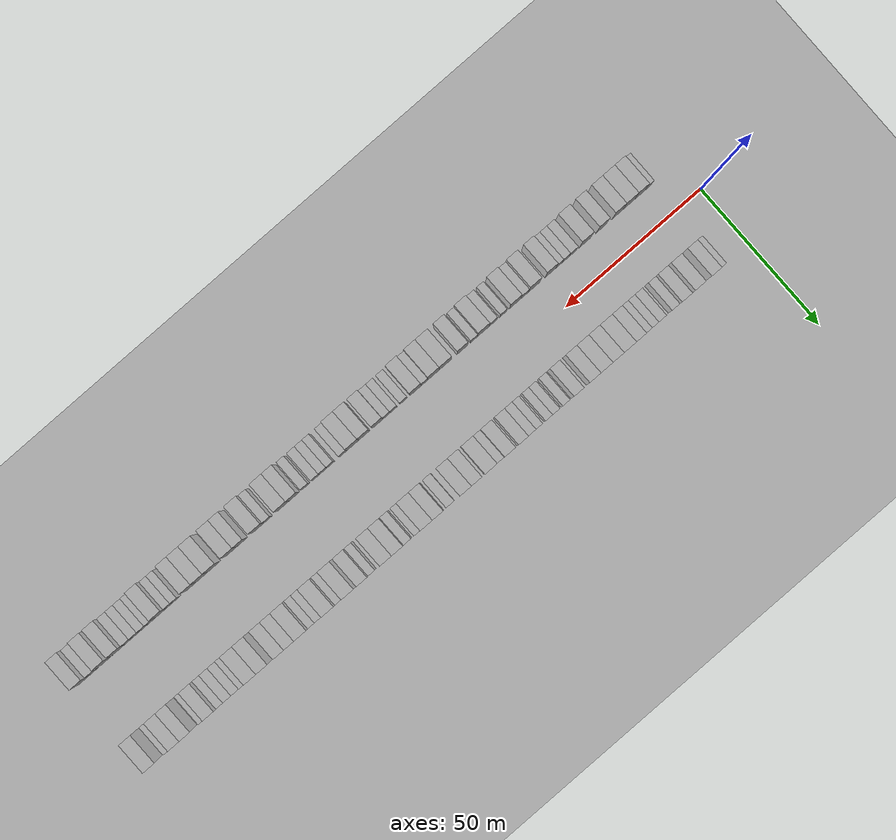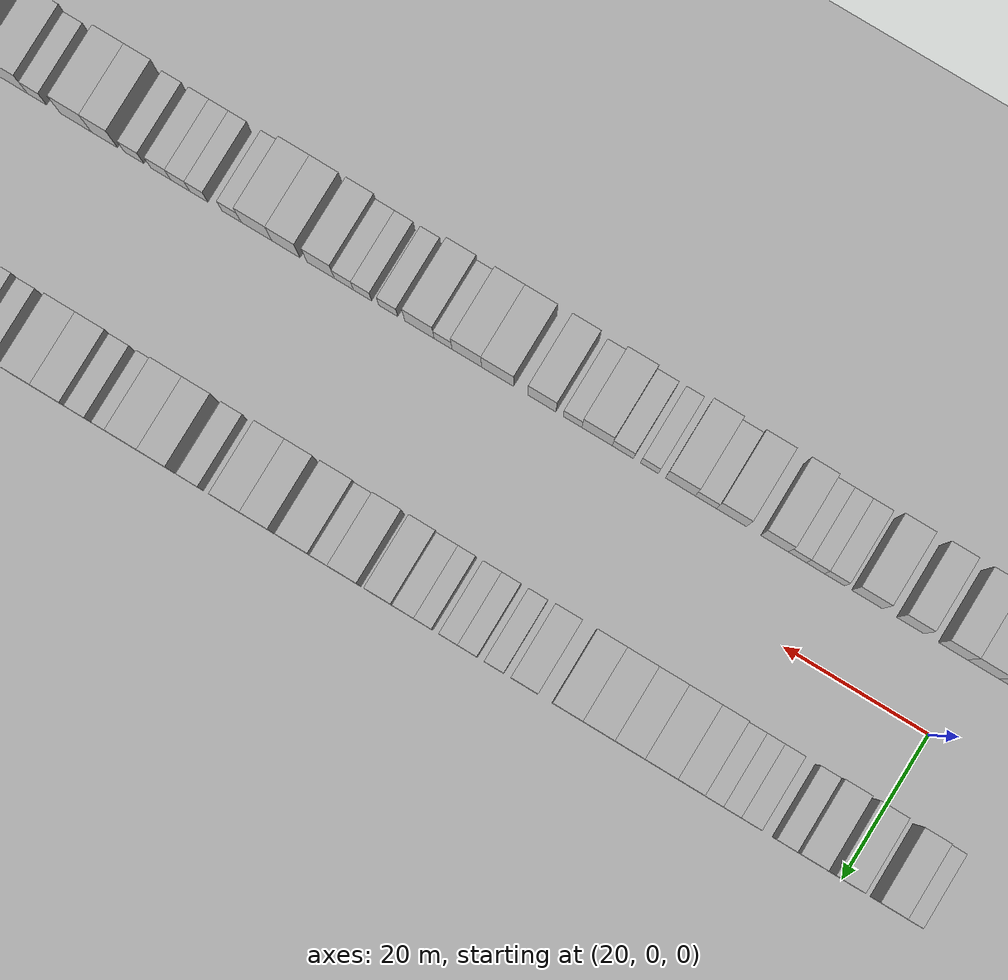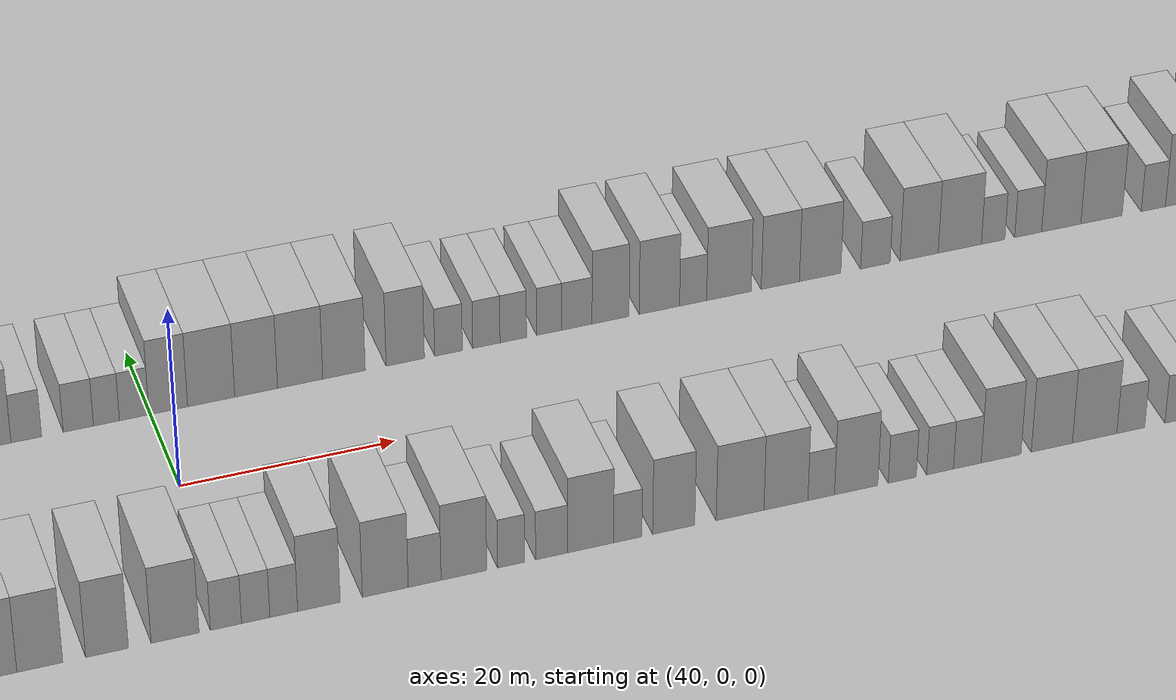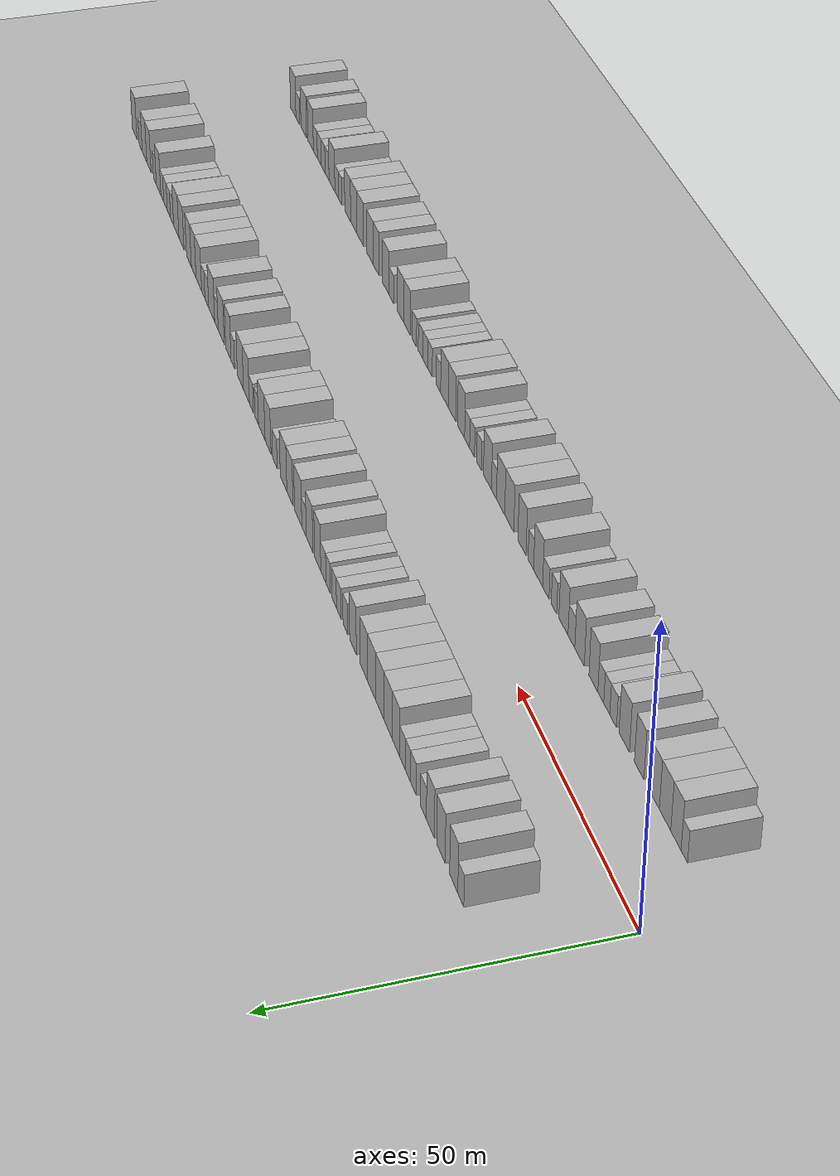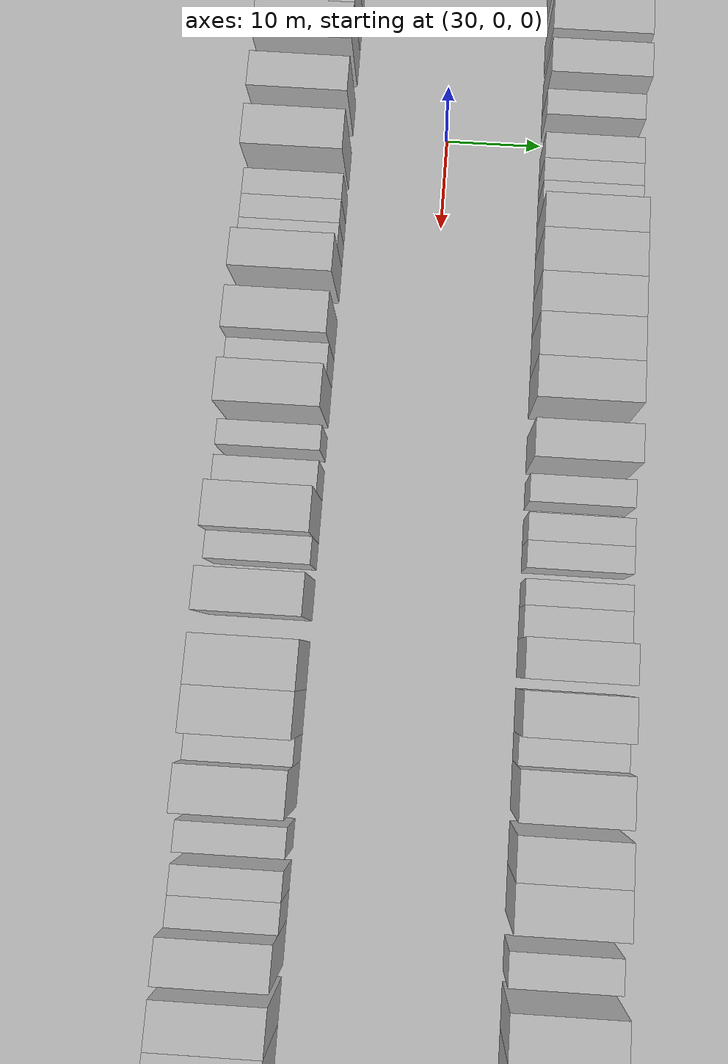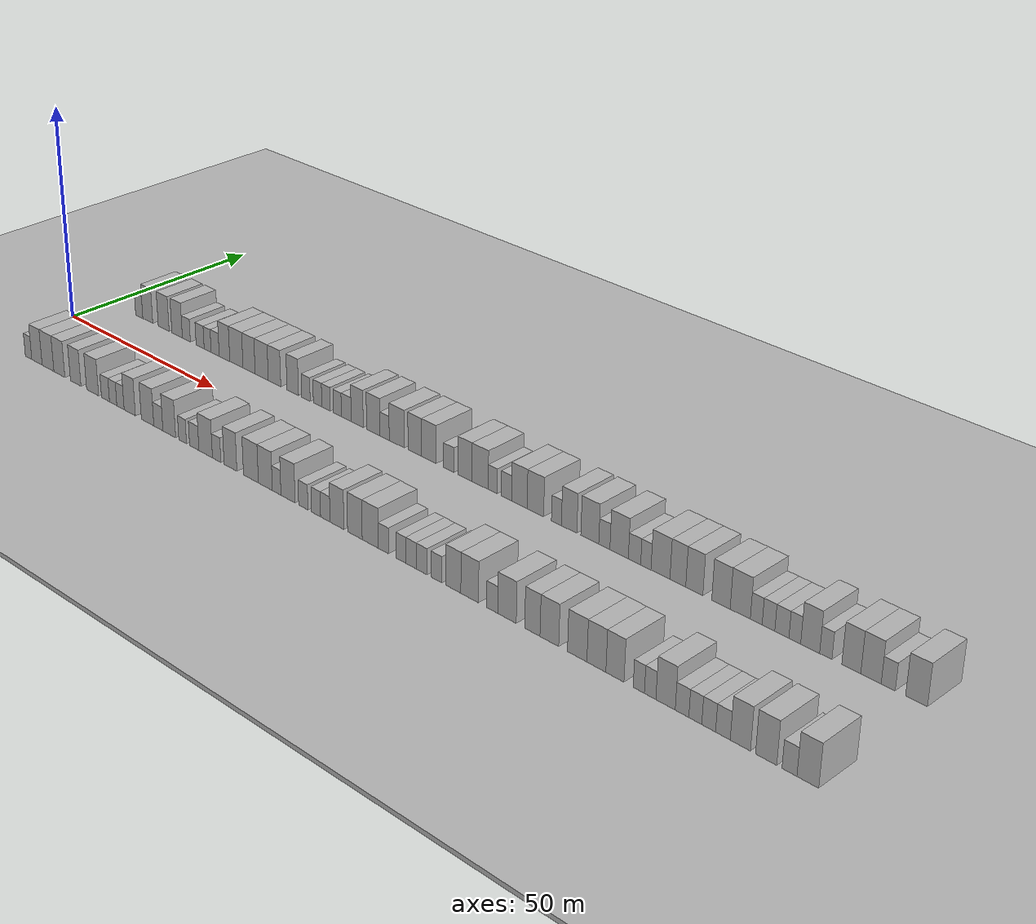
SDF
<?xml version="1.0" encoding="utf-8"?>

<sdf version="1.6">

   <world name="default">

      <gui fullscreen="0">

         <camera name="user_camera">

            <pose>-15 0 4.57585 0 0 0</pose>

            <view_controller>orbit</view_controller>

         </camera>

      </gui>

      <scene>

         <sky>

           <clouds>

             <speed>12</speed>

           </clouds>

         </sky>

         <ambient>0.4 0.4 0.4 1</ambient>

         <background>0.7 0.7 0.7 1</background>

         <shadows>1</shadows>

      </scene>

      <gravity>0 0 -9.8066</gravity>

      <magnetic_field>6e-06 2.3e-05 -4.2e-05</magnetic_field>

      <physics default="0" name="default_physics" type="ode">

         <ode>

            <solver>

               <type>quick</type>

               <iters>10</iters>

               <sor>1.0</sor>

               <use_dynamic_moi_rescaling>0</use_dynamic_moi_rescaling>

            </solver>

            <constraints>

               <cfm>0</cfm>

               <erp>0.2</erp>

               <contact_max_correcting_vel>100</contact_max_correcting_vel>

               <contact_surface_layer>0.001</contact_surface_layer>

            </constraints>

         </ode>

         <max_step_size>0.004</max_step_size>

         <real_time_factor>1</real_time_factor>

         <real_time_update_rate>250</real_time_update_rate>

      </physics>

      <light name="sun" type="directional">

         <cast_shadows>1</cast_shadows>

         <pose>0 0 10 0 0 0</pose>

         <diffuse>0.8 0.8 0.8 1</diffuse>

         <specular>0.2 0.2 0.2 1</specular>

         <attenuation>

            <range>1000</range>

            <constant>0.9</constant>

            <linear>0.01</linear>

            <quadratic>0.001</quadratic>

         </attenuation>

         <direction>-0.5 0.1 -0.9</direction>

      </light>

      <include>

         <name>ground_plane_1</name>

         <uri>model://HANNAS_ground_plane</uri>

         <pose>0 0 0  0 0 0</pose>

      </include>

      <include>

         <name>ground_plane_2</name>

         <uri>model://HANNAS_ground_plane</uri>

         <pose>100 0 0  0 0 0</pose>

      </include>

      <model name="building_1">

         <static>1</static>

         <pose frame="">11.3128 15.0000 0 0.000000 0.000000 1.570796</pose>

         <link name="link">

            <pose frame="">0 0 3.00 0 0 0</pose>

            <collision name="collision">

               <geometry>

                  <box>

                     <size>10.0000 2.6256 6.0000</size>

                  </box>

               </geometry>

               <max_contacts>10</max_contacts>

               <surface>

                  <contact>

                     <ode/>

                  </contact>

                  <bounce/>

                  <friction>

                     <torsional>

                        <ode/>

                     </torsional>

                     <ode/>

                  </friction>

               </surface>

            </collision>

            <visual name="visual">

               <cast_shadows>0</cast_shadows>

               <geometry>

                  <box>

                     <size>10.0000 2.6256 6.0000</size>

                  </box>

               </geometry>

               <material>

                  <script>

                     <uri>model://HANNAS_wall/materials/scripts</uri>

                     <uri>model://HANNAS_wall/materials/textures</uri>

                     <name>vrc/HANNAS_wall</name>

                  </script>

               </material>

            </visual>

            <self_collide>0</self_collide>

            <enable_wind>0</enable_wind>

            <kinematic>0</kinematic>

         </link>

      </model>

      <model name="building_2">

         <static>1</static>

         <pose frame="">14.4493 15.0000 0 0.000000 0.000000 1.570796</pose>

         <link name="link">

            <pose frame="">0 0 4.50 0 0 0</pose>

            <collision name="collision">

               <geometry>

                  <box>

                     <size>10.0000 3.6474 9.0000</size>

                  </box>

               </geometry>

               <max_contacts>10</max_contacts>

               <surface>

                  <contact>

                     <ode/>

                  </contact>

                  <bounce/>

                  <friction>

                     <torsional>

                        <ode/>

                     </torsional>

                     <ode/>

                  </friction>

               </surface>

            </collision>

            <visual name="visual">

               <cast_shadows>0</cast_shadows>

               <geometry>

                  <box>

                     <size>10.0000 3.6474 9.0000</size>

                  </box>

               </geometry>

               <material>

                  <script>

                     <uri>model://HANNAS_wall/materials/scripts</uri>

                     <uri>model://HANNAS_wall/materials/textures</uri>

                     <name>vrc/HANNAS_wall</name>

                  </script>

               </material>

            </visual>

            <self_collide>0</self_collide>

            <enable_wind>0</enable_wind>

            <kinematic>0</kinematic>

         </link>

      </model>

      <model name="building_3">

         <static>1</static>

         <pose frame="">20.2281 15.0000 0 0.000000 0.000000 1.570796</pose>

         <link name="link">

            <pose frame="">0 0 4.50 0 0 0</pose>

            <collision name="collision">

               <geometry>

                  <box>

                     <size>10.0000 3.9103 9.0000</size>

                  </box>

               </geometry>

               <max_contacts>10</max_contacts>

               <surface>

                  <contact>

                     <ode/>

                  </contact>

                  <bounce/>

                  <friction>

                     <torsional>

                        <ode/>

                     </torsional>

                     <ode/>

                  </friction>

               </surface>

            </collision>

            <visual name="visual">

               <cast_shadows>0</cast_shadows>

               <geometry>

                  <box>

                     <size>10.0000 3.9103 9.0000</size>

                  </box>

               </geometry>

               <material>

                  <script>

                     <uri>model://HANNAS_wall/materials/scripts</uri>

                     <uri>model://HANNAS_wall/materials/textures</uri>

                     <name>vrc/HANNAS_wall</name>

                  </script>

               </material>

            </visual>

            <self_collide>0</self_collide>

            <enable_wind>0</enable_wind>

            <kinematic>0</kinematic>

         </link>

      </model>

      <model name="building_4">

         <static>1</static>

         <pose frame="">25.0439 15.0000 0 0.000000 0.000000 1.570796</pose>

         <link name="link">

            <pose frame="">0 0 4.50 0 0 0</pose>

            <collision name="collision">

               <geometry>

                  <box>

                     <size>10.0000 3.7213 9.0000</size>

                  </box>

               </geometry>

               <max_contacts>10</max_contacts>

               <surface>

                  <contact>

                     <ode/>

                  </contact>

                  <bounce/>

                  <friction>

                     <torsional>

                        <ode/>

                     </torsional>

                     <ode/>

                  </friction>

               </surface>

            </collision>

            <visual name="visual">

               <cast_shadows>0</cast_shadows>

               <geometry>

                  <box>

                     <size>10.0000 3.7213 9.0000</size>

                  </box>

               </geometry>

               <material>

                  <script>

                     <uri>model://HANNAS_wall/materials/scripts</uri>

                     <uri>model://HANNAS_wall/materials/textures</uri>

                     <name>vrc/HANNAS_wall</name>

                  </script>

               </material>

            </visual>

            <self_collide>0</self_collide>

            <enable_wind>0</enable_wind>

            <kinematic>0</kinematic>

         </link>

      </model>

      <model name="building_5">

         <static>1</static>

         <pose frame="">28.3138 15.0000 0 0.000000 0.000000 1.570796</pose>

         <link name="link">

            <pose frame="">0 0 3.00 0 0 0</pose>

            <collision name="collision">

               <geometry>

                  <box>

                     <size>10.0000 2.8185 6.0000</size>

                  </box>

               </geometry>

               <max_contacts>10</max_contacts>

               <surface>

                  <contact>

                     <ode/>

                  </contact>

                  <bounce/>

                  <friction>

                     <torsional>

                        <ode/>

                     </torsional>

                     <ode/>

                  </friction>

               </surface>

            </collision>

            <visual name="visual">

               <cast_shadows>0</cast_shadows>

               <geometry>

                  <box>

                     <size>10.0000 2.8185 6.0000</size>

                  </box>

               </geometry>

               <material>

                  <script>

                     <uri>model://HANNAS_wall/materials/scripts</uri>

                     <uri>model://HANNAS_wall/materials/textures</uri>

                     <name>vrc/HANNAS_wall</name>

                  </script>

               </material>

            </visual>

            <self_collide>0</self_collide>

            <enable_wind>0</enable_wind>

            <kinematic>0</kinematic>

         </link>

      </model>

      <model name="building_6">

         <static>1</static>

         <pose frame="">33.1258 15.0000 0 0.000000 0.000000 1.570796</pose>

         <link name="link">

            <pose frame="">0 0 3.00 0 0 0</pose>

            <collision name="collision">

               <geometry>

                  <box>

                     <size>10.0000 2.8056 6.0000</size>

                  </box>

               </geometry>

               <max_contacts>10</max_contacts>

               <surface>

                  <contact>

                     <ode/>

                  </contact>

                  <bounce/>

                  <friction>

                     <torsional>

                        <ode/>

                     </torsional>

                     <ode/>

                  </friction>

               </surface>

            </collision>

            <visual name="visual">

               <cast_shadows>0</cast_shadows>

               <geometry>

                  <box>

                     <size>10.0000 2.8056 6.0000</size>

                  </box>

               </geometry>

               <material>

                  <script>

                     <uri>model://HANNAS_wall/materials/scripts</uri>

                     <uri>model://HANNAS_wall/materials/textures</uri>

                     <name>vrc/HANNAS_wall</name>

                  </script>

               </material>

            </visual>

            <self_collide>0</self_collide>

            <enable_wind>0</enable_wind>

            <kinematic>0</kinematic>

         </link>

      </model>

      <model name="building_7">

         <static>1</static>

         <pose frame="">35.7378 15.0000 0 0.000000 0.000000 1.570796</pose>

         <link name="link">

            <pose frame="">0 0 3.00 0 0 0</pose>

            <collision name="collision">

               <geometry>

                  <box>

                     <size>10.0000 2.4183 6.0000</size>

                  </box>

               </geometry>

               <max_contacts>10</max_contacts>

               <surface>

                  <contact>

                     <ode/>

                  </contact>

                  <bounce/>

                  <friction>

                     <torsional>

                        <ode/>

                     </torsional>

                     <ode/>

                  </friction>

               </surface>

            </collision>

            <visual name="visual">

               <cast_shadows>0</cast_shadows>

               <geometry>

                  <box>

                     <size>10.0000 2.4183 6.0000</size>

                  </box>

               </geometry>

               <material>

                  <script>

                     <uri>model://HANNAS_wall/materials/scripts</uri>

                     <uri>model://HANNAS_wall/materials/textures</uri>

                     <name>vrc/HANNAS_wall</name>

                  </script>

               </material>

            </visual>

            <self_collide>0</self_collide>

            <enable_wind>0</enable_wind>

            <kinematic>0</kinematic>

         </link>

      </model>

      <model name="building_8">

         <static>1</static>

         <pose frame="">38.3267 15.0000 0 0.000000 0.000000 1.570796</pose>

         <link name="link">

            <pose frame="">0 0 3.00 0 0 0</pose>

            <collision name="collision">

               <geometry>

                  <box>

                     <size>10.0000 2.7596 6.0000</size>

                  </box>

               </geometry>

               <max_contacts>10</max_contacts>

               <surface>

                  <contact>

                     <ode/>

                  </contact>

                  <bounce/>

                  <friction>

                     <torsional>

                        <ode/>

                     </torsional>

                     <ode/>

                  </friction>

               </surface>

            </collision>

            <visual name="visual">

               <cast_shadows>0</cast_shadows>

               <geometry>

                  <box>

                     <size>10.0000 2.7596 6.0000</size>

                  </box>

               </geometry>

               <material>

                  <script>

                     <uri>model://HANNAS_wall/materials/scripts</uri>

                     <uri>model://HANNAS_wall/materials/textures</uri>

                     <name>vrc/HANNAS_wall</name>

                  </script>

               </material>

            </visual>

            <self_collide>0</self_collide>

            <enable_wind>0</enable_wind>

            <kinematic>0</kinematic>

         </link>

      </model>

      <model name="building_9">

         <static>1</static>

         <pose frame="">41.5138 15.0000 0 0.000000 0.000000 1.570796</pose>

         <link name="link">

            <pose frame="">0 0 4.50 0 0 0</pose>

            <collision name="collision">

               <geometry>

                  <box>

                     <size>10.0000 3.6146 9.0000</size>

                  </box>

               </geometry>

               <max_contacts>10</max_contacts>

               <surface>

                  <contact>

                     <ode/>

                  </contact>

                  <bounce/>

                  <friction>

                     <torsional>

                        <ode/>

                     </torsional>

                     <ode/>

                  </friction>

               </surface>

            </collision>

            <visual name="visual">

               <cast_shadows>0</cast_shadows>

               <geometry>

                  <box>

                     <size>10.0000 3.6146 9.0000</size>

                  </box>

               </geometry>

               <material>

                  <script>

                     <uri>model://HANNAS_wall/materials/scripts</uri>

                     <uri>model://HANNAS_wall/materials/textures</uri>

                     <name>vrc/HANNAS_wall</name>

                  </script>

               </material>

            </visual>

            <self_collide>0</self_collide>

            <enable_wind>0</enable_wind>

            <kinematic>0</kinematic>

         </link>

      </model>

      <model name="building_10">

         <static>1</static>

         <pose frame="">45.5383 15.0000 0 0.000000 0.000000 1.570796</pose>

         <link name="link">

            <pose frame="">0 0 4.50 0 0 0</pose>

            <collision name="collision">

               <geometry>

                  <box>

                     <size>10.0000 4.4344 9.0000</size>

                  </box>

               </geometry>

               <max_contacts>10</max_contacts>

               <surface>

                  <contact>

                     <ode/>

                  </contact>

                  <bounce/>

                  <friction>

                     <torsional>

                        <ode/>

                     </torsional>

                     <ode/>

                  </friction>

               </surface>

            </collision>

            <visual name="visual">

               <cast_shadows>0</cast_shadows>

               <geometry>

                  <box>

                     <size>10.0000 4.4344 9.0000</size>

                  </box>

               </geometry>

               <material>

                  <script>

                     <uri>model://HANNAS_wall/materials/scripts</uri>

                     <uri>model://HANNAS_wall/materials/textures</uri>

                     <name>vrc/HANNAS_wall</name>

                  </script>

               </material>

            </visual>

            <self_collide>0</self_collide>

            <enable_wind>0</enable_wind>

            <kinematic>0</kinematic>

         </link>

      </model>

      <model name="building_11">

         <static>1</static>

         <pose frame="">49.7776 15.0000 0 0.000000 0.000000 1.570796</pose>

         <link name="link">

            <pose frame="">0 0 4.50 0 0 0</pose>

            <collision name="collision">

               <geometry>

                  <box>

                     <size>10.0000 4.0441 9.0000</size>

                  </box>

               </geometry>

               <max_contacts>10</max_contacts>

               <surface>

                  <contact>

                     <ode/>

                  </contact>

                  <bounce/>

                  <friction>

                     <torsional>

                        <ode/>

                     </torsional>

                     <ode/>

                  </friction>

               </surface>

            </collision>

            <visual name="visual">

               <cast_shadows>0</cast_shadows>

               <geometry>

                  <box>

                     <size>10.0000 4.0441 9.0000</size>

                  </box>

               </geometry>

               <material>

                  <script>

                     <uri>model://HANNAS_wall/materials/scripts</uri>

                     <uri>model://HANNAS_wall/materials/textures</uri>

                     <name>vrc/HANNAS_wall</name>

                  </script>

               </material>

            </visual>

            <self_collide>0</self_collide>

            <enable_wind>0</enable_wind>

            <kinematic>0</kinematic>

         </link>

      </model>

      <model name="building_12">

         <static>1</static>

         <pose frame="">53.9528 15.0000 0 0.000000 0.000000 1.570796</pose>

         <link name="link">

            <pose frame="">0 0 4.50 0 0 0</pose>

            <collision name="collision">

               <geometry>

                  <box>

                     <size>10.0000 4.3062 9.0000</size>

                  </box>

               </geometry>

               <max_contacts>10</max_contacts>

               <surface>

                  <contact>

                     <ode/>

                  </contact>

                  <bounce/>

                  <friction>

                     <torsional>

                        <ode/>

                     </torsional>

                     <ode/>

                  </friction>

               </surface>

            </collision>

            <visual name="visual">

               <cast_shadows>0</cast_shadows>

               <geometry>

                  <box>

                     <size>10.0000 4.3062 9.0000</size>

                  </box>

               </geometry>

               <material>

                  <script>

                     <uri>model://HANNAS_wall/materials/scripts</uri>

                     <uri>model://HANNAS_wall/materials/textures</uri>

                     <name>vrc/HANNAS_wall</name>

                  </script>

               </material>

            </visual>

            <self_collide>0</self_collide>

            <enable_wind>0</enable_wind>

            <kinematic>0</kinematic>

         </link>

      </model>

      <model name="building_13">

         <static>1</static>

         <pose frame="">58.1287 15.0000 0 0.000000 0.000000 1.570796</pose>

         <link name="link">

            <pose frame="">0 0 4.50 0 0 0</pose>

            <collision name="collision">

               <geometry>

                  <box>

                     <size>10.0000 4.0456 9.0000</size>

                  </box>

               </geometry>

               <max_contacts>10</max_contacts>

               <surface>

                  <contact>

                     <ode/>

                  </contact>

                  <bounce/>

                  <friction>

                     <torsional>

                        <ode/>

                     </torsional>

                     <ode/>

                  </friction>

               </surface>

            </collision>

            <visual name="visual">

               <cast_shadows>0</cast_shadows>

               <geometry>

                  <box>

                     <size>10.0000 4.0456 9.0000</size>

                  </box>

               </geometry>

               <material>

                  <script>

                     <uri>model://HANNAS_wall/materials/scripts</uri>

                     <uri>model://HANNAS_wall/materials/textures</uri>

                     <name>vrc/HANNAS_wall</name>

                  </script>

               </material>

            </visual>

            <self_collide>0</self_collide>

            <enable_wind>0</enable_wind>

            <kinematic>0</kinematic>

         </link>

      </model>

      <model name="building_14">

         <static>1</static>

         <pose frame="">63.9874 15.0000 0 0.000000 0.000000 1.570796</pose>

         <link name="link">

            <pose frame="">0 0 4.50 0 0 0</pose>

            <collision name="collision">

               <geometry>

                  <box>

                     <size>10.0000 3.6719 9.0000</size>

                  </box>

               </geometry>

               <max_contacts>10</max_contacts>

               <surface>

                  <contact>

                     <ode/>

                  </contact>

                  <bounce/>

                  <friction>

                     <torsional>

                        <ode/>

                     </torsional>

                     <ode/>

                  </friction>

               </surface>

            </collision>

            <visual name="visual">

               <cast_shadows>0</cast_shadows>

               <geometry>

                  <box>

                     <size>10.0000 3.6719 9.0000</size>

                  </box>

               </geometry>

               <material>

                  <script>

                     <uri>model://HANNAS_wall/materials/scripts</uri>

                     <uri>model://HANNAS_wall/materials/textures</uri>

                     <name>vrc/HANNAS_wall</name>

                  </script>

               </material>

            </visual>

            <self_collide>0</self_collide>

            <enable_wind>0</enable_wind>

            <kinematic>0</kinematic>

         </link>

      </model>

      <model name="building_15">

         <static>1</static>

         <pose frame="">68.1576 15.0000 0 0.000000 0.000000 1.570796</pose>

         <link name="link">

            <pose frame="">0 0 3.00 0 0 0</pose>

            <collision name="collision">

               <geometry>

                  <box>

                     <size>10.0000 2.6684 6.0000</size>

                  </box>

               </geometry>

               <max_contacts>10</max_contacts>

               <surface>

                  <contact>

                     <ode/>

                  </contact>

                  <bounce/>

                  <friction>

                     <torsional>

                        <ode/>

                     </torsional>

                     <ode/>

                  </friction>

               </surface>

            </collision>

            <visual name="visual">

               <cast_shadows>0</cast_shadows>

               <geometry>

                  <box>

                     <size>10.0000 2.6684 6.0000</size>

                  </box>

               </geometry>

               <material>

                  <script>

                     <uri>model://HANNAS_wall/materials/scripts</uri>

                     <uri>model://HANNAS_wall/materials/textures</uri>

                     <name>vrc/HANNAS_wall</name>

                  </script>

               </material>

            </visual>

            <self_collide>0</self_collide>

            <enable_wind>0</enable_wind>

            <kinematic>0</kinematic>

         </link>

      </model>

      <model name="building_16">

         <static>1</static>

         <pose frame="">71.8129 15.0000 0 0.000000 0.000000 1.570796</pose>

         <link name="link">

            <pose frame="">0 0 3.00 0 0 0</pose>

            <collision name="collision">

               <geometry>

                  <box>

                     <size>10.0000 2.6423 6.0000</size>

                  </box>

               </geometry>

               <max_contacts>10</max_contacts>

               <surface>

                  <contact>

                     <ode/>

                  </contact>

                  <bounce/>

                  <friction>

                     <torsional>

                        <ode/>

                     </torsional>

                     <ode/>

                  </friction>

               </surface>

            </collision>

            <visual name="visual">

               <cast_shadows>0</cast_shadows>

               <geometry>

                  <box>

                     <size>10.0000 2.6423 6.0000</size>

                  </box>

               </geometry>

               <material>

                  <script>

                     <uri>model://HANNAS_wall/materials/scripts</uri>

                     <uri>model://HANNAS_wall/materials/textures</uri>

                     <name>vrc/HANNAS_wall</name>

                  </script>

               </material>

            </visual>

            <self_collide>0</self_collide>

            <enable_wind>0</enable_wind>

            <kinematic>0</kinematic>

         </link>

      </model>

      <model name="building_17">

         <static>1</static>

         <pose frame="">74.4219 15.0000 0 0.000000 0.000000 1.570796</pose>

         <link name="link">

            <pose frame="">0 0 3.00 0 0 0</pose>

            <collision name="collision">

               <geometry>

                  <box>

                     <size>10.0000 2.5757 6.0000</size>

                  </box>

               </geometry>

               <max_contacts>10</max_contacts>

               <surface>

                  <contact>

                     <ode/>

                  </contact>

                  <bounce/>

                  <friction>

                     <torsional>

                        <ode/>

                     </torsional>

                     <ode/>

                  </friction>

               </surface>

            </collision>

            <visual name="visual">

               <cast_shadows>0</cast_shadows>

               <geometry>

                  <box>

                     <size>10.0000 2.5757 6.0000</size>

                  </box>

               </geometry>

               <material>

                  <script>

                     <uri>model://HANNAS_wall/materials/scripts</uri>

                     <uri>model://HANNAS_wall/materials/textures</uri>

                     <name>vrc/HANNAS_wall</name>

                  </script>

               </material>

            </visual>

            <self_collide>0</self_collide>

            <enable_wind>0</enable_wind>

            <kinematic>0</kinematic>

         </link>

      </model>

      <model name="building_18">

         <static>1</static>

         <pose frame="">77.9255 15.0000 0 0.000000 0.000000 1.570796</pose>

         <link name="link">

            <pose frame="">0 0 3.00 0 0 0</pose>

            <collision name="collision">

               <geometry>

                  <box>

                     <size>10.0000 2.4316 6.0000</size>

                  </box>

               </geometry>

               <max_contacts>10</max_contacts>

               <surface>

                  <contact>

                     <ode/>

                  </contact>

                  <bounce/>

                  <friction>

                     <torsional>

                        <ode/>

                     </torsional>

                     <ode/>

                  </friction>

               </surface>

            </collision>

            <visual name="visual">

               <cast_shadows>0</cast_shadows>

               <geometry>

                  <box>

                     <size>10.0000 2.4316 6.0000</size>

                  </box>

               </geometry>

               <material>

                  <script>

                     <uri>model://HANNAS_wall/materials/scripts</uri>

                     <uri>model://HANNAS_wall/materials/textures</uri>

                     <name>vrc/HANNAS_wall</name>

                  </script>

               </material>

            </visual>

            <self_collide>0</self_collide>

            <enable_wind>0</enable_wind>

            <kinematic>0</kinematic>

         </link>

      </model>

      <model name="building_19">

         <static>1</static>

         <pose frame="">80.6324 15.0000 0 0.000000 0.000000 1.570796</pose>

         <link name="link">

            <pose frame="">0 0 3.00 0 0 0</pose>

            <collision name="collision">

               <geometry>

                  <box>

                     <size>10.0000 2.9821 6.0000</size>

                  </box>

               </geometry>

               <max_contacts>10</max_contacts>

               <surface>

                  <contact>

                     <ode/>

                  </contact>

                  <bounce/>

                  <friction>

                     <torsional>

                        <ode/>

                     </torsional>

                     <ode/>

                  </friction>

               </surface>

            </collision>

            <visual name="visual">

               <cast_shadows>0</cast_shadows>

               <geometry>

                  <box>

                     <size>10.0000 2.9821 6.0000</size>

                  </box>

               </geometry>

               <material>

                  <script>

                     <uri>model://HANNAS_wall/materials/scripts</uri>

                     <uri>model://HANNAS_wall/materials/textures</uri>

                     <name>vrc/HANNAS_wall</name>

                  </script>

               </material>

            </visual>

            <self_collide>0</self_collide>

            <enable_wind>0</enable_wind>

            <kinematic>0</kinematic>

         </link>

      </model>

      <model name="building_20">

         <static>1</static>

         <pose frame="">83.9403 15.0000 0 0.000000 0.000000 1.570796</pose>

         <link name="link">

            <pose frame="">0 0 4.50 0 0 0</pose>

            <collision name="collision">

               <geometry>

                  <box>

                     <size>10.0000 3.6337 9.0000</size>

                  </box>

               </geometry>

               <max_contacts>10</max_contacts>

               <surface>

                  <contact>

                     <ode/>

                  </contact>

                  <bounce/>

                  <friction>

                     <torsional>

                        <ode/>

                     </torsional>

                     <ode/>

                  </friction>

               </surface>

            </collision>

            <visual name="visual">

               <cast_shadows>0</cast_shadows>

               <geometry>

                  <box>

                     <size>10.0000 3.6337 9.0000</size>

                  </box>

               </geometry>

               <material>

                  <script>

                     <uri>model://HANNAS_wall/materials/scripts</uri>

                     <uri>model://HANNAS_wall/materials/textures</uri>

                     <name>vrc/HANNAS_wall</name>

                  </script>

               </material>

            </visual>

            <self_collide>0</self_collide>

            <enable_wind>0</enable_wind>

            <kinematic>0</kinematic>

         </link>

      </model>

      <model name="building_21">

         <static>1</static>

         <pose frame="">88.7528 15.0000 0 0.000000 0.000000 1.570796</pose>

         <link name="link">

            <pose frame="">0 0 4.50 0 0 0</pose>

            <collision name="collision">

               <geometry>

                  <box>

                     <size>10.0000 3.9913 9.0000</size>

                  </box>

               </geometry>

               <max_contacts>10</max_contacts>

               <surface>

                  <contact>

                     <ode/>

                  </contact>

                  <bounce/>

                  <friction>

                     <torsional>

                        <ode/>

                     </torsional>

                     <ode/>

                  </friction>

               </surface>

            </collision>

            <visual name="visual">

               <cast_shadows>0</cast_shadows>

               <geometry>

                  <box>

                     <size>10.0000 3.9913 9.0000</size>

                  </box>

               </geometry>

               <material>

                  <script>

                     <uri>model://HANNAS_wall/materials/scripts</uri>

                     <uri>model://HANNAS_wall/materials/textures</uri>

                     <name>vrc/HANNAS_wall</name>

                  </script>

               </material>

            </visual>

            <self_collide>0</self_collide>

            <enable_wind>0</enable_wind>

            <kinematic>0</kinematic>

         </link>

      </model>

      <model name="building_22">

         <static>1</static>

         <pose frame="">92.0898 15.0000 0 0.000000 0.000000 1.570796</pose>

         <link name="link">

            <pose frame="">0 0 3.00 0 0 0</pose>

            <collision name="collision">

               <geometry>

                  <box>

                     <size>10.0000 2.6827 6.0000</size>

                  </box>

               </geometry>

               <max_contacts>10</max_contacts>

               <surface>

                  <contact>

                     <ode/>

                  </contact>

                  <bounce/>

                  <friction>

                     <torsional>

                        <ode/>

                     </torsional>

                     <ode/>

                  </friction>

               </surface>

            </collision>

            <visual name="visual">

               <cast_shadows>0</cast_shadows>

               <geometry>

                  <box>

                     <size>10.0000 2.6827 6.0000</size>

                  </box>

               </geometry>

               <material>

                  <script>

                     <uri>model://HANNAS_wall/materials/scripts</uri>

                     <uri>model://HANNAS_wall/materials/textures</uri>

                     <name>vrc/HANNAS_wall</name>

                  </script>

               </material>

            </visual>

            <self_collide>0</self_collide>

            <enable_wind>0</enable_wind>

            <kinematic>0</kinematic>

         </link>

      </model>

      <model name="building_23">

         <static>1</static>

         <pose frame="">95.6516 15.0000 0 0.000000 0.000000 1.570796</pose>

         <link name="link">

            <pose frame="">0 0 4.50 0 0 0</pose>

            <collision name="collision">

               <geometry>

                  <box>

                     <size>10.0000 4.4408 9.0000</size>

                  </box>

               </geometry>

               <max_contacts>10</max_contacts>

               <surface>

                  <contact>

                     <ode/>

                  </contact>

                  <bounce/>

                  <friction>

                     <torsional>

                        <ode/>

                     </torsional>

                     <ode/>

                  </friction>

               </surface>

            </collision>

            <visual name="visual">

               <cast_shadows>0</cast_shadows>

               <geometry>

                  <box>

                     <size>10.0000 4.4408 9.0000</size>

                  </box>

               </geometry>

               <material>

                  <script>

                     <uri>model://HANNAS_wall/materials/scripts</uri>

                     <uri>model://HANNAS_wall/materials/textures</uri>

                     <name>vrc/HANNAS_wall</name>

                  </script>

               </material>

            </visual>

            <self_collide>0</self_collide>

            <enable_wind>0</enable_wind>

            <kinematic>0</kinematic>

         </link>

      </model>

      <model name="building_24">

         <static>1</static>

         <pose frame="">100.7843 15.0000 0 0.000000 0.000000 1.570796</pose>

         <link name="link">

            <pose frame="">0 0 4.50 0 0 0</pose>

            <collision name="collision">

               <geometry>

                  <box>

                     <size>10.0000 3.8246 9.0000</size>

                  </box>

               </geometry>

               <max_contacts>10</max_contacts>

               <surface>

                  <contact>

                     <ode/>

                  </contact>

                  <bounce/>

                  <friction>

                     <torsional>

                        <ode/>

                     </torsional>

                     <ode/>

                  </friction>

               </surface>

            </collision>

            <visual name="visual">

               <cast_shadows>0</cast_shadows>

               <geometry>

                  <box>

                     <size>10.0000 3.8246 9.0000</size>

                  </box>

               </geometry>

               <material>

                  <script>

                     <uri>model://HANNAS_wall/materials/scripts</uri>

                     <uri>model://HANNAS_wall/materials/textures</uri>

                     <name>vrc/HANNAS_wall</name>

                  </script>

               </material>

            </visual>

            <self_collide>0</self_collide>

            <enable_wind>0</enable_wind>

            <kinematic>0</kinematic>

         </link>

      </model>

      <model name="building_25">

         <static>1</static>

         <pose frame="">104.7812 15.0000 0 0.000000 0.000000 1.570796</pose>

         <link name="link">

            <pose frame="">0 0 4.50 0 0 0</pose>

            <collision name="collision">

               <geometry>

                  <box>

                     <size>10.0000 4.1693 9.0000</size>

                  </box>

               </geometry>

               <max_contacts>10</max_contacts>

               <surface>

                  <contact>

                     <ode/>

                  </contact>

                  <bounce/>

                  <friction>

                     <torsional>

                        <ode/>

                     </torsional>

                     <ode/>

                  </friction>

               </surface>

            </collision>

            <visual name="visual">

               <cast_shadows>0</cast_shadows>

               <geometry>

                  <box>

                     <size>10.0000 4.1693 9.0000</size>

                  </box>

               </geometry>

               <material>

                  <script>

                     <uri>model://HANNAS_wall/materials/scripts</uri>

                     <uri>model://HANNAS_wall/materials/textures</uri>

                     <name>vrc/HANNAS_wall</name>

                  </script>

               </material>

            </visual>

            <self_collide>0</self_collide>

            <enable_wind>0</enable_wind>

            <kinematic>0</kinematic>

         </link>

      </model>

      <model name="building_26">

         <static>1</static>

         <pose frame="">110.3599 15.0000 0 0.000000 0.000000 1.570796</pose>

         <link name="link">

            <pose frame="">0 0 3.00 0 0 0</pose>

            <collision name="collision">

               <geometry>

                  <box>

                     <size>10.0000 2.9880 6.0000</size>

                  </box>

               </geometry>

               <max_contacts>10</max_contacts>

               <surface>

                  <contact>

                     <ode/>

                  </contact>

                  <bounce/>

                  <friction>

                     <torsional>

                        <ode/>

                     </torsional>

                     <ode/>

                  </friction>

               </surface>

            </collision>

            <visual name="visual">

               <cast_shadows>0</cast_shadows>

               <geometry>

                  <box>

                     <size>10.0000 2.9880 6.0000</size>

                  </box>

               </geometry>

               <material>

                  <script>

                     <uri>model://HANNAS_wall/materials/scripts</uri>

                     <uri>model://HANNAS_wall/materials/textures</uri>

                     <name>vrc/HANNAS_wall</name>

                  </script>

               </material>

            </visual>

            <self_collide>0</self_collide>

            <enable_wind>0</enable_wind>

            <kinematic>0</kinematic>

         </link>

      </model>

      <model name="building_27">

         <static>1</static>

         <pose frame="">114.8001 15.0000 0 0.000000 0.000000 1.570796</pose>

         <link name="link">

            <pose frame="">0 0 4.50 0 0 0</pose>

            <collision name="collision">

               <geometry>

                  <box>

                     <size>10.0000 3.8925 9.0000</size>

                  </box>

               </geometry>

               <max_contacts>10</max_contacts>

               <surface>

                  <contact>

                     <ode/>

                  </contact>

                  <bounce/>

                  <friction>

                     <torsional>

                        <ode/>

                     </torsional>

                     <ode/>

                  </friction>

               </surface>

            </collision>

            <visual name="visual">

               <cast_shadows>0</cast_shadows>

               <geometry>

                  <box>

                     <size>10.0000 3.8925 9.0000</size>

                  </box>

               </geometry>

               <material>

                  <script>

                     <uri>model://HANNAS_wall/materials/scripts</uri>

                     <uri>model://HANNAS_wall/materials/textures</uri>

                     <name>vrc/HANNAS_wall</name>

                  </script>

               </material>

            </visual>

            <self_collide>0</self_collide>

            <enable_wind>0</enable_wind>

            <kinematic>0</kinematic>

         </link>

      </model>

      <model name="building_28">

         <static>1</static>

         <pose frame="">118.9540 15.0000 0 0.000000 0.000000 1.570796</pose>

         <link name="link">

            <pose frame="">0 0 4.50 0 0 0</pose>

            <collision name="collision">

               <geometry>

                  <box>

                     <size>10.0000 4.4151 9.0000</size>

                  </box>

               </geometry>

               <max_contacts>10</max_contacts>

               <surface>

                  <contact>

                     <ode/>

                  </contact>

                  <bounce/>

                  <friction>

                     <torsional>

                        <ode/>

                     </torsional>

                     <ode/>

                  </friction>

               </surface>

            </collision>

            <visual name="visual">

               <cast_shadows>0</cast_shadows>

               <geometry>

                  <box>

                     <size>10.0000 4.4151 9.0000</size>

                  </box>

               </geometry>

               <material>

                  <script>

                     <uri>model://HANNAS_wall/materials/scripts</uri>

                     <uri>model://HANNAS_wall/materials/textures</uri>

                     <name>vrc/HANNAS_wall</name>

                  </script>

               </material>

            </visual>

            <self_collide>0</self_collide>

            <enable_wind>0</enable_wind>

            <kinematic>0</kinematic>

         </link>

      </model>

      <model name="building_29">

         <static>1</static>

         <pose frame="">122.3704 15.0000 0 0.000000 0.000000 1.570796</pose>

         <link name="link">

            <pose frame="">0 0 3.00 0 0 0</pose>

            <collision name="collision">

               <geometry>

                  <box>

                     <size>10.0000 2.4178 6.0000</size>

                  </box>

               </geometry>

               <max_contacts>10</max_contacts>

               <surface>

                  <contact>

                     <ode/>

                  </contact>

                  <bounce/>

                  <friction>

                     <torsional>

                        <ode/>

                     </torsional>

                     <ode/>

                  </friction>

               </surface>

            </collision>

            <visual name="visual">

               <cast_shadows>0</cast_shadows>

               <geometry>

                  <box>

                     <size>10.0000 2.4178 6.0000</size>

                  </box>

               </geometry>

               <material>

                  <script>

                     <uri>model://HANNAS_wall/materials/scripts</uri>

                     <uri>model://HANNAS_wall/materials/textures</uri>

                     <name>vrc/HANNAS_wall</name>

                  </script>

               </material>

            </visual>

            <self_collide>0</self_collide>

            <enable_wind>0</enable_wind>

            <kinematic>0</kinematic>

         </link>

      </model>

      <model name="building_30">

         <static>1</static>

         <pose frame="">125.9705 15.0000 0 0.000000 0.000000 1.570796</pose>

         <link name="link">

            <pose frame="">0 0 3.00 0 0 0</pose>

            <collision name="collision">

               <geometry>

                  <box>

                     <size>10.0000 2.7824 6.0000</size>

                  </box>

               </geometry>

               <max_contacts>10</max_contacts>

               <surface>

                  <contact>

                     <ode/>

                  </contact>

                  <bounce/>

                  <friction>

                     <torsional>

                        <ode/>

                     </torsional>

                     <ode/>

                  </friction>

               </surface>

            </collision>

            <visual name="visual">

               <cast_shadows>0</cast_shadows>

               <geometry>

                  <box>

                     <size>10.0000 2.7824 6.0000</size>

                  </box>

               </geometry>

               <material>

                  <script>

                     <uri>model://HANNAS_wall/materials/scripts</uri>

                     <uri>model://HANNAS_wall/materials/textures</uri>

                     <name>vrc/HANNAS_wall</name>

                  </script>

               </material>

            </visual>

            <self_collide>0</self_collide>

            <enable_wind>0</enable_wind>

            <kinematic>0</kinematic>

         </link>

      </model>

      <model name="building_31">

         <static>1</static>

         <pose frame="">129.3902 15.0000 0 0.000000 0.000000 1.570796</pose>

         <link name="link">

            <pose frame="">0 0 4.50 0 0 0</pose>

            <collision name="collision">

               <geometry>

                  <box>

                     <size>10.0000 4.0570 9.0000</size>

                  </box>

               </geometry>

               <max_contacts>10</max_contacts>

               <surface>

                  <contact>

                     <ode/>

                  </contact>

                  <bounce/>

                  <friction>

                     <torsional>

                        <ode/>

                     </torsional>

                     <ode/>

                  </friction>

               </surface>

            </collision>

            <visual name="visual">

               <cast_shadows>0</cast_shadows>

               <geometry>

                  <box>

                     <size>10.0000 4.0570 9.0000</size>

                  </box>

               </geometry>

               <material>

                  <script>

                     <uri>model://HANNAS_wall/materials/scripts</uri>

                     <uri>model://HANNAS_wall/materials/textures</uri>

                     <name>vrc/HANNAS_wall</name>

                  </script>

               </material>

            </visual>

            <self_collide>0</self_collide>

            <enable_wind>0</enable_wind>

            <kinematic>0</kinematic>

         </link>

      </model>

      <model name="building_32">

         <static>1</static>

         <pose frame="">133.5595 15.0000 0 0.000000 0.000000 1.570796</pose>

         <link name="link">

            <pose frame="">0 0 4.50 0 0 0</pose>

            <collision name="collision">

               <geometry>

                  <box>

                     <size>10.0000 4.2816 9.0000</size>

                  </box>

               </geometry>

               <max_contacts>10</max_contacts>

               <surface>

                  <contact>

                     <ode/>

                  </contact>

                  <bounce/>

                  <friction>

                     <torsional>

                        <ode/>

                     </torsional>

                     <ode/>

                  </friction>

               </surface>

            </collision>

            <visual name="visual">

               <cast_shadows>0</cast_shadows>

               <geometry>

                  <box>

                     <size>10.0000 4.2816 9.0000</size>

                  </box>

               </geometry>

               <material>

                  <script>

                     <uri>model://HANNAS_wall/materials/scripts</uri>

                     <uri>model://HANNAS_wall/materials/textures</uri>

                     <name>vrc/HANNAS_wall</name>

                  </script>

               </material>

            </visual>

            <self_collide>0</self_collide>

            <enable_wind>0</enable_wind>

            <kinematic>0</kinematic>

         </link>

      </model>

      <model name="building_33">

         <static>1</static>

         <pose frame="">138.9618 15.0000 0 0.000000 0.000000 1.570796</pose>

         <link name="link">

            <pose frame="">0 0 3.00 0 0 0</pose>

            <collision name="collision">

               <geometry>

                  <box>

                     <size>10.0000 2.5230 6.0000</size>

                  </box>

               </geometry>

               <max_contacts>10</max_contacts>

               <surface>

                  <contact>

                     <ode/>

                  </contact>

                  <bounce/>

                  <friction>

                     <torsional>

                        <ode/>

                     </torsional>

                     <ode/>

                  </friction>

               </surface>

            </collision>

            <visual name="visual">

               <cast_shadows>0</cast_shadows>

               <geometry>

                  <box>

                     <size>10.0000 2.5230 6.0000</size>

                  </box>

               </geometry>

               <material>

                  <script>

                     <uri>model://HANNAS_wall/materials/scripts</uri>

                     <uri>model://HANNAS_wall/materials/textures</uri>

                     <name>vrc/HANNAS_wall</name>

                  </script>

               </material>

            </visual>

            <self_collide>0</self_collide>

            <enable_wind>0</enable_wind>

            <kinematic>0</kinematic>

         </link>

      </model>

      <model name="building_34">

         <static>1</static>

         <pose frame="">142.1640 15.0000 0 0.000000 0.000000 1.570796</pose>

         <link name="link">

            <pose frame="">0 0 4.50 0 0 0</pose>

            <collision name="collision">

               <geometry>

                  <box>

                     <size>10.0000 3.8814 9.0000</size>

                  </box>

               </geometry>

               <max_contacts>10</max_contacts>

               <surface>

                  <contact>

                     <ode/>

                  </contact>

                  <bounce/>

                  <friction>

                     <torsional>

                        <ode/>

                     </torsional>

                     <ode/>

                  </friction>

               </surface>

            </collision>

            <visual name="visual">

               <cast_shadows>0</cast_shadows>

               <geometry>

                  <box>

                     <size>10.0000 3.8814 9.0000</size>

                  </box>

               </geometry>

               <material>

                  <script>

                     <uri>model://HANNAS_wall/materials/scripts</uri>

                     <uri>model://HANNAS_wall/materials/textures</uri>

                     <name>vrc/HANNAS_wall</name>

                  </script>

               </material>

            </visual>

            <self_collide>0</self_collide>

            <enable_wind>0</enable_wind>

            <kinematic>0</kinematic>

         </link>

      </model>

      <model name="building_35">

         <static>1</static>

         <pose frame="">147.3182 15.0000 0 0.000000 0.000000 1.570796</pose>

         <link name="link">

            <pose frame="">0 0 4.50 0 0 0</pose>

            <collision name="collision">

               <geometry>

                  <box>

                     <size>10.0000 4.4270 9.0000</size>

                  </box>

               </geometry>

               <max_contacts>10</max_contacts>

               <surface>

                  <contact>

                     <ode/>

                  </contact>

                  <bounce/>

                  <friction>

                     <torsional>

                        <ode/>

                     </torsional>

                     <ode/>

                  </friction>

               </surface>

            </collision>

            <visual name="visual">

               <cast_shadows>0</cast_shadows>

               <geometry>

                  <box>

                     <size>10.0000 4.4270 9.0000</size>

                  </box>

               </geometry>

               <material>

                  <script>

                     <uri>model://HANNAS_wall/materials/scripts</uri>

                     <uri>model://HANNAS_wall/materials/textures</uri>

                     <name>vrc/HANNAS_wall</name>

                  </script>

               </material>

            </visual>

            <self_collide>0</self_collide>

            <enable_wind>0</enable_wind>

            <kinematic>0</kinematic>

         </link>

      </model>

      <model name="building_36">

         <static>1</static>

         <pose frame="">150.8977 15.0000 0 0.000000 0.000000 1.570796</pose>

         <link name="link">

            <pose frame="">0 0 3.00 0 0 0</pose>

            <collision name="collision">

               <geometry>

                  <box>

                     <size>10.0000 2.7321 6.0000</size>

                  </box>

               </geometry>

               <max_contacts>10</max_contacts>

               <surface>

                  <contact>

                     <ode/>

                  </contact>

                  <bounce/>

                  <friction>

                     <torsional>

                        <ode/>

                     </torsional>

                     <ode/>

                  </friction>

               </surface>

            </collision>

            <visual name="visual">

               <cast_shadows>0</cast_shadows>

               <geometry>

                  <box>

                     <size>10.0000 2.7321 6.0000</size>

                  </box>

               </geometry>

               <material>

                  <script>

                     <uri>model://HANNAS_wall/materials/scripts</uri>

                     <uri>model://HANNAS_wall/materials/textures</uri>

                     <name>vrc/HANNAS_wall</name>

                  </script>

               </material>

            </visual>

            <self_collide>0</self_collide>

            <enable_wind>0</enable_wind>

            <kinematic>0</kinematic>

         </link>

      </model>

      <model name="building_37">

         <static>1</static>

         <pose frame="">154.4824 15.0000 0 0.000000 0.000000 1.570796</pose>

         <link name="link">

            <pose frame="">0 0 4.50 0 0 0</pose>

            <collision name="collision">

               <geometry>

                  <box>

                     <size>10.0000 4.4373 9.0000</size>

                  </box>

               </geometry>

               <max_contacts>10</max_contacts>

               <surface>

                  <contact>

                     <ode/>

                  </contact>

                  <bounce/>

                  <friction>

                     <torsional>

                        <ode/>

                     </torsional>

                     <ode/>

                  </friction>

               </surface>

            </collision>

            <visual name="visual">

               <cast_shadows>0</cast_shadows>

               <geometry>

                  <box>

                     <size>10.0000 4.4373 9.0000</size>

                  </box>

               </geometry>

               <material>

                  <script>

                     <uri>model://HANNAS_wall/materials/scripts</uri>

                     <uri>model://HANNAS_wall/materials/textures</uri>

                     <name>vrc/HANNAS_wall</name>

                  </script>

               </material>

            </visual>

            <self_collide>0</self_collide>

            <enable_wind>0</enable_wind>

            <kinematic>0</kinematic>

         </link>

      </model>

      <model name="building_38">

         <static>1</static>

         <pose frame="">158.1775 15.0000 0 0.000000 0.000000 1.570796</pose>

         <link name="link">

            <pose frame="">0 0 3.00 0 0 0</pose>

            <collision name="collision">

               <geometry>

                  <box>

                     <size>10.0000 2.9529 6.0000</size>

                  </box>

               </geometry>

               <max_contacts>10</max_contacts>

               <surface>

                  <contact>

                     <ode/>

                  </contact>

                  <bounce/>

                  <friction>

                     <torsional>

                        <ode/>

                     </torsional>

                     <ode/>

                  </friction>

               </surface>

            </collision>

            <visual name="visual">

               <cast_shadows>0</cast_shadows>

               <geometry>

                  <box>

                     <size>10.0000 2.9529 6.0000</size>

                  </box>

               </geometry>

               <material>

                  <script>

                     <uri>model://HANNAS_wall/materials/scripts</uri>

                     <uri>model://HANNAS_wall/materials/textures</uri>

                     <name>vrc/HANNAS_wall</name>

                  </script>

               </material>

            </visual>

            <self_collide>0</self_collide>

            <enable_wind>0</enable_wind>

            <kinematic>0</kinematic>

         </link>

      </model>

      <model name="building_39">

         <static>1</static>

         <pose frame="">160.8714 15.0000 0 0.000000 0.000000 1.570796</pose>

         <link name="link">

            <pose frame="">0 0 3.00 0 0 0</pose>

            <collision name="collision">

               <geometry>

                  <box>

                     <size>10.0000 2.4348 6.0000</size>

                  </box>

               </geometry>

               <max_contacts>10</max_contacts>

               <surface>

                  <contact>

                     <ode/>

                  </contact>

                  <bounce/>

                  <friction>

                     <torsional>

                        <ode/>

                     </torsional>

                     <ode/>

                  </friction>

               </surface>

            </collision>

            <visual name="visual">

               <cast_shadows>0</cast_shadows>

               <geometry>

                  <box>

                     <size>10.0000 2.4348 6.0000</size>

                  </box>

               </geometry>

               <material>

                  <script>

                     <uri>model://HANNAS_wall/materials/scripts</uri>

                     <uri>model://HANNAS_wall/materials/textures</uri>

                     <name>vrc/HANNAS_wall</name>

                  </script>

               </material>

            </visual>

            <self_collide>0</self_collide>

            <enable_wind>0</enable_wind>

            <kinematic>0</kinematic>

         </link>

      </model>

      <model name="building_40">

         <static>1</static>

         <pose frame="">164.3016 15.0000 0 0.000000 0.000000 1.570796</pose>

         <link name="link">

            <pose frame="">0 0 4.50 0 0 0</pose>

            <collision name="collision">

               <geometry>

                  <box>

                     <size>10.0000 4.4256 9.0000</size>

                  </box>

               </geometry>

               <max_contacts>10</max_contacts>

               <surface>

                  <contact>

                     <ode/>

                  </contact>

                  <bounce/>

                  <friction>

                     <torsional>

                        <ode/>

                     </torsional>

                     <ode/>

                  </friction>

               </surface>

            </collision>

            <visual name="visual">

               <cast_shadows>0</cast_shadows>

               <geometry>

                  <box>

                     <size>10.0000 4.4256 9.0000</size>

                  </box>

               </geometry>

               <material>

                  <script>

                     <uri>model://HANNAS_wall/materials/scripts</uri>

                     <uri>model://HANNAS_wall/materials/textures</uri>

                     <name>vrc/HANNAS_wall</name>

                  </script>

               </material>

            </visual>

            <self_collide>0</self_collide>

            <enable_wind>0</enable_wind>

            <kinematic>0</kinematic>

         </link>

      </model>

      <model name="building_41">

         <static>1</static>

         <pose frame="">168.3324 15.0000 0 0.000000 0.000000 1.570796</pose>

         <link name="link">

            <pose frame="">0 0 4.50 0 0 0</pose>

            <collision name="collision">

               <geometry>

                  <box>

                     <size>10.0000 3.6360 9.0000</size>

                  </box>

               </geometry>

               <max_contacts>10</max_contacts>

               <surface>

                  <contact>

                     <ode/>

                  </contact>

                  <bounce/>

                  <friction>

                     <torsional>

                        <ode/>

                     </torsional>

                     <ode/>

                  </friction>

               </surface>

            </collision>

            <visual name="visual">

               <cast_shadows>0</cast_shadows>

               <geometry>

                  <box>

                     <size>10.0000 3.6360 9.0000</size>

                  </box>

               </geometry>

               <material>

                  <script>

                     <uri>model://HANNAS_wall/materials/scripts</uri>

                     <uri>model://HANNAS_wall/materials/textures</uri>

                     <name>vrc/HANNAS_wall</name>

                  </script>

               </material>

            </visual>

            <self_collide>0</self_collide>

            <enable_wind>0</enable_wind>

            <kinematic>0</kinematic>

         </link>

      </model>

      <model name="building_42">

         <static>1</static>

         <pose frame="">172.1010 15.0000 0 0.000000 0.000000 1.570796</pose>

         <link name="link">

            <pose frame="">0 0 4.50 0 0 0</pose>

            <collision name="collision">

               <geometry>

                  <box>

                     <size>10.0000 3.9010 9.0000</size>

                  </box>

               </geometry>

               <max_contacts>10</max_contacts>

               <surface>

                  <contact>

                     <ode/>

                  </contact>

                  <bounce/>

                  <friction>

                     <torsional>

                        <ode/>

                     </torsional>

                     <ode/>

                  </friction>

               </surface>

            </collision>

            <visual name="visual">

               <cast_shadows>0</cast_shadows>

               <geometry>

                  <box>

                     <size>10.0000 3.9010 9.0000</size>

                  </box>

               </geometry>

               <material>

                  <script>

                     <uri>model://HANNAS_wall/materials/scripts</uri>

                     <uri>model://HANNAS_wall/materials/textures</uri>

                     <name>vrc/HANNAS_wall</name>

                  </script>

               </material>

            </visual>

            <self_collide>0</self_collide>

            <enable_wind>0</enable_wind>

            <kinematic>0</kinematic>

         </link>

      </model>

      <model name="building_43">

         <static>1</static>

         <pose frame="">178.1021 15.0000 0 0.000000 0.000000 1.570796</pose>

         <link name="link">

            <pose frame="">0 0 4.50 0 0 0</pose>

            <collision name="collision">

               <geometry>

                  <box>

                     <size>10.0000 4.1012 9.0000</size>

                  </box>

               </geometry>

               <max_contacts>10</max_contacts>

               <surface>

                  <contact>

                     <ode/>

                  </contact>

                  <bounce/>

                  <friction>

                     <torsional>

                        <ode/>

                     </torsional>

                     <ode/>

                  </friction>

               </surface>

            </collision>

            <visual name="visual">

               <cast_shadows>0</cast_shadows>

               <geometry>

                  <box>

                     <size>10.0000 4.1012 9.0000</size>

                  </box>

               </geometry>

               <material>

                  <script>

                     <uri>model://HANNAS_wall/materials/scripts</uri>

                     <uri>model://HANNAS_wall/materials/textures</uri>

                     <name>vrc/HANNAS_wall</name>

                  </script>

               </material>

            </visual>

            <self_collide>0</self_collide>

            <enable_wind>0</enable_wind>

            <kinematic>0</kinematic>

         </link>

      </model>

      <model name="building_44">

         <static>1</static>

         <pose frame="">182.3665 15.0000 0 0.000000 0.000000 1.570796</pose>

         <link name="link">

            <pose frame="">0 0 4.50 0 0 0</pose>

            <collision name="collision">

               <geometry>

                  <box>

                     <size>10.0000 4.4276 9.0000</size>

                  </box>

               </geometry>

               <max_contacts>10</max_contacts>

               <surface>

                  <contact>

                     <ode/>

                  </contact>

                  <bounce/>

                  <friction>

                     <torsional>

                        <ode/>

                     </torsional>

                     <ode/>

                  </friction>

               </surface>

            </collision>

            <visual name="visual">

               <cast_shadows>0</cast_shadows>

               <geometry>

                  <box>

                     <size>10.0000 4.4276 9.0000</size>

                  </box>

               </geometry>

               <material>

                  <script>

                     <uri>model://HANNAS_wall/materials/scripts</uri>

                     <uri>model://HANNAS_wall/materials/textures</uri>

                     <name>vrc/HANNAS_wall</name>

                  </script>

               </material>

            </visual>

            <self_collide>0</self_collide>

            <enable_wind>0</enable_wind>

            <kinematic>0</kinematic>

         </link>

      </model>

      <model name="building_45">

         <static>1</static>

         <pose frame="">185.8606 15.0000 0 0.000000 0.000000 1.570796</pose>

         <link name="link">

            <pose frame="">0 0 3.00 0 0 0</pose>

            <collision name="collision">

               <geometry>

                  <box>

                     <size>10.0000 2.5606 6.0000</size>

                  </box>

               </geometry>

               <max_contacts>10</max_contacts>

               <surface>

                  <contact>

                     <ode/>

                  </contact>

                  <bounce/>

                  <friction>

                     <torsional>

                        <ode/>

                     </torsional>

                     <ode/>

                  </friction>

               </surface>

            </collision>

            <visual name="visual">

               <cast_shadows>0</cast_shadows>

               <geometry>

                  <box>

                     <size>10.0000 2.5606 6.0000</size>

                  </box>

               </geometry>

               <material>

                  <script>

                     <uri>model://HANNAS_wall/materials/scripts</uri>

                     <uri>model://HANNAS_wall/materials/textures</uri>

                     <name>vrc/HANNAS_wall</name>

                  </script>

               </material>

            </visual>

            <self_collide>0</self_collide>

            <enable_wind>0</enable_wind>

            <kinematic>0</kinematic>

         </link>

      </model>

      <model name="building_46">

         <static>1</static>

         <pose frame="">188.5053 15.0000 0 0.000000 0.000000 1.570796</pose>

         <link name="link">

            <pose frame="">0 0 3.00 0 0 0</pose>

            <collision name="collision">

               <geometry>

                  <box>

                     <size>10.0000 2.7289 6.0000</size>

                  </box>

               </geometry>

               <max_contacts>10</max_contacts>

               <surface>

                  <contact>

                     <ode/>

                  </contact>

                  <bounce/>

                  <friction>

                     <torsional>

                        <ode/>

                     </torsional>

                     <ode/>

                  </friction>

               </surface>

            </collision>

            <visual name="visual">

               <cast_shadows>0</cast_shadows>

               <geometry>

                  <box>

                     <size>10.0000 2.7289 6.0000</size>

                  </box>

               </geometry>

               <material>

                  <script>

                     <uri>model://HANNAS_wall/materials/scripts</uri>

                     <uri>model://HANNAS_wall/materials/textures</uri>

                     <name>vrc/HANNAS_wall</name>

                  </script>

               </material>

            </visual>

            <self_collide>0</self_collide>

            <enable_wind>0</enable_wind>

            <kinematic>0</kinematic>

         </link>

      </model>

      <model name="building_47">

         <static>1</static>

         <pose frame="">191.3675 15.0000 0 0.000000 0.000000 1.570796</pose>

         <link name="link">

            <pose frame="">0 0 3.00 0 0 0</pose>

            <collision name="collision">

               <geometry>

                  <box>

                     <size>10.0000 2.9955 6.0000</size>

                  </box>

               </geometry>

               <max_contacts>10</max_contacts>

               <surface>

                  <contact>

                     <ode/>

                  </contact>

                  <bounce/>

                  <friction>

                     <torsional>

                        <ode/>

                     </torsional>

                     <ode/>

                  </friction>

               </surface>

            </collision>

            <visual name="visual">

               <cast_shadows>0</cast_shadows>

               <geometry>

                  <box>

                     <size>10.0000 2.9955 6.0000</size>

                  </box>

               </geometry>

               <material>

                  <script>

                     <uri>model://HANNAS_wall/materials/scripts</uri>

                     <uri>model://HANNAS_wall/materials/textures</uri>

                     <name>vrc/HANNAS_wall</name>

                  </script>

               </material>

            </visual>

            <self_collide>0</self_collide>

            <enable_wind>0</enable_wind>

            <kinematic>0</kinematic>

         </link>

      </model>

      <model name="building_48">

         <static>1</static>

         <pose frame="">194.1044 15.0000 0 0.000000 0.000000 1.570796</pose>

         <link name="link">

            <pose frame="">0 0 3.00 0 0 0</pose>

            <collision name="collision">

               <geometry>

                  <box>

                     <size>10.0000 2.4783 6.0000</size>

                  </box>

               </geometry>

               <max_contacts>10</max_contacts>

               <surface>

                  <contact>

                     <ode/>

                  </contact>

                  <bounce/>

                  <friction>

                     <torsional>

                        <ode/>

                     </torsional>

                     <ode/>

                  </friction>

               </surface>

            </collision>

            <visual name="visual">

               <cast_shadows>0</cast_shadows>

               <geometry>

                  <box>

                     <size>10.0000 2.4783 6.0000</size>

                  </box>

               </geometry>

               <material>

                  <script>

                     <uri>model://HANNAS_wall/materials/scripts</uri>

                     <uri>model://HANNAS_wall/materials/textures</uri>

                     <name>vrc/HANNAS_wall</name>

                  </script>

               </material>

            </visual>

            <self_collide>0</self_collide>

            <enable_wind>0</enable_wind>

            <kinematic>0</kinematic>

         </link>

      </model>

      <model name="building_49">

         <static>1</static>

         <pose frame="">197.3221 15.0000 0 0.000000 0.000000 1.570796</pose>

         <link name="link">

            <pose frame="">0 0 4.50 0 0 0</pose>

            <collision name="collision">

               <geometry>

                  <box>

                     <size>10.0000 3.9571 9.0000</size>

                  </box>

               </geometry>

               <max_contacts>10</max_contacts>

               <surface>

                  <contact>

                     <ode/>

                  </contact>

                  <bounce/>

                  <friction>

                     <torsional>

                        <ode/>

                     </torsional>

                     <ode/>

                  </friction>

               </surface>

            </collision>

            <visual name="visual">

               <cast_shadows>0</cast_shadows>

               <geometry>

                  <box>

                     <size>10.0000 3.9571 9.0000</size>

                  </box>

               </geometry>

               <material>

                  <script>

                     <uri>model://HANNAS_wall/materials/scripts</uri>

                     <uri>model://HANNAS_wall/materials/textures</uri>

                     <name>vrc/HANNAS_wall</name>

                  </script>

               </material>

            </visual>

            <self_collide>0</self_collide>

            <enable_wind>0</enable_wind>

            <kinematic>0</kinematic>

         </link>

      </model>

      <model name="building_50">

         <static>1</static>

         <pose frame="">200.5690 15.0000 0 0.000000 0.000000 1.570796</pose>

         <link name="link">

            <pose frame="">0 0 3.00 0 0 0</pose>

            <collision name="collision">

               <geometry>

                  <box>

                     <size>10.0000 2.5367 6.0000</size>

                  </box>

               </geometry>

               <max_contacts>10</max_contacts>

               <surface>

                  <contact>

                     <ode/>

                  </contact>

                  <bounce/>

                  <friction>

                     <torsional>

                        <ode/>

                     </torsional>

                     <ode/>

                  </friction>

               </surface>

            </collision>

            <visual name="visual">

               <cast_shadows>0</cast_shadows>

               <geometry>

                  <box>

                     <size>10.0000 2.5367 6.0000</size>

                  </box>

               </geometry>

               <material>

                  <script>

                     <uri>model://HANNAS_wall/materials/scripts</uri>

                     <uri>model://HANNAS_wall/materials/textures</uri>

                     <name>vrc/HANNAS_wall</name>

                  </script>

               </material>

            </visual>

            <self_collide>0</self_collide>

            <enable_wind>0</enable_wind>

            <kinematic>0</kinematic>

         </link>

      </model>

      <model name="building_51">

         <static>1</static>

         <pose frame="">205.7570 15.0000 0 0.000000 0.000000 1.570796</pose>

         <link name="link">

            <pose frame="">0 0 4.50 0 0 0</pose>

            <collision name="collision">

               <geometry>

                  <box>

                     <size>10.0000 3.8393 9.0000</size>

                  </box>

               </geometry>

               <max_contacts>10</max_contacts>

               <surface>

                  <contact>

                     <ode/>

                  </contact>

                  <bounce/>

                  <friction>

                     <torsional>

                        <ode/>

                     </torsional>

                     <ode/>

                  </friction>

               </surface>

            </collision>

            <visual name="visual">

               <cast_shadows>0</cast_shadows>

               <geometry>

                  <box>

                     <size>10.0000 3.8393 9.0000</size>

                  </box>

               </geometry>

               <material>

                  <script>

                     <uri>model://HANNAS_wall/materials/scripts</uri>

                     <uri>model://HANNAS_wall/materials/textures</uri>

                     <name>vrc/HANNAS_wall</name>

                  </script>

               </material>

            </visual>

            <self_collide>0</self_collide>

            <enable_wind>0</enable_wind>

            <kinematic>0</kinematic>

         </link>

      </model>

      <model name="building_52">

         <static>1</static>

         <pose frame="">209.7104 15.0000 0 0.000000 0.000000 1.570796</pose>

         <link name="link">

            <pose frame="">0 0 4.50 0 0 0</pose>

            <collision name="collision">

               <geometry>

                  <box>

                     <size>10.0000 4.0676 9.0000</size>

                  </box>

               </geometry>

               <max_contacts>10</max_contacts>

               <surface>

                  <contact>

                     <ode/>

                  </contact>

                  <bounce/>

                  <friction>

                     <torsional>

                        <ode/>

                     </torsional>

                     <ode/>

                  </friction>

               </surface>

            </collision>

            <visual name="visual">

               <cast_shadows>0</cast_shadows>

               <geometry>

                  <box>

                     <size>10.0000 4.0676 9.0000</size>

                  </box>

               </geometry>

               <material>

                  <script>

                     <uri>model://HANNAS_wall/materials/scripts</uri>

                     <uri>model://HANNAS_wall/materials/textures</uri>

                     <name>vrc/HANNAS_wall</name>

                  </script>

               </material>

            </visual>

            <self_collide>0</self_collide>

            <enable_wind>0</enable_wind>

            <kinematic>0</kinematic>

         </link>

      </model>

      <model name="building_53">

         <static>1</static>

         <pose frame="">213.1324 15.0000 0 0.000000 0.000000 1.570796</pose>

         <link name="link">

            <pose frame="">0 0 3.00 0 0 0</pose>

            <collision name="collision">

               <geometry>

                  <box>

                     <size>10.0000 2.7764 6.0000</size>

                  </box>

               </geometry>

               <max_contacts>10</max_contacts>

               <surface>

                  <contact>

                     <ode/>

                  </contact>

                  <bounce/>

                  <friction>

                     <torsional>

                        <ode/>

                     </torsional>

                     <ode/>

                  </friction>

               </surface>

            </collision>

            <visual name="visual">

               <cast_shadows>0</cast_shadows>

               <geometry>

                  <box>

                     <size>10.0000 2.7764 6.0000</size>

                  </box>

               </geometry>

               <material>

                  <script>

                     <uri>model://HANNAS_wall/materials/scripts</uri>

                     <uri>model://HANNAS_wall/materials/textures</uri>

                     <name>vrc/HANNAS_wall</name>

                  </script>

               </material>

            </visual>

            <self_collide>0</self_collide>

            <enable_wind>0</enable_wind>

            <kinematic>0</kinematic>

         </link>

      </model>

      <model name="building_54">

         <static>1</static>

         <pose frame="">218.6330 15.0000 0 0.000000 0.000000 1.570796</pose>

         <link name="link">

            <pose frame="">0 0 4.50 0 0 0</pose>

            <collision name="collision">

               <geometry>

                  <box>

                     <size>10.0000 4.2248 9.0000</size>

                  </box>

               </geometry>

               <max_contacts>10</max_contacts>

               <surface>

                  <contact>

                     <ode/>

                  </contact>

                  <bounce/>

                  <friction>

                     <torsional>

                        <ode/>

                     </torsional>

                     <ode/>

                  </friction>

               </surface>

            </collision>

            <visual name="visual">

               <cast_shadows>0</cast_shadows>

               <geometry>

                  <box>

                     <size>10.0000 4.2248 9.0000</size>

                  </box>

               </geometry>

               <material>

                  <script>

                     <uri>model://HANNAS_wall/materials/scripts</uri>

                     <uri>model://HANNAS_wall/materials/textures</uri>

                     <name>vrc/HANNAS_wall</name>

                  </script>

               </material>

            </visual>

            <self_collide>0</self_collide>

            <enable_wind>0</enable_wind>

            <kinematic>0</kinematic>

         </link>

      </model>

      <model name="building_55">

         <static>1</static>

         <pose frame="">11.2029 -15.0000 0 0.000000 0.000000 1.570796</pose>

         <link name="link">

            <pose frame="">0 0 3.00 0 0 0</pose>

            <collision name="collision">

               <geometry>

                  <box>

                     <size>10.0000 2.4059 6.0000</size>

                  </box>

               </geometry>

               <max_contacts>10</max_contacts>

               <surface>

                  <contact>

                     <ode/>

                  </contact>

                  <bounce/>

                  <friction>

                     <torsional>

                        <ode/>

                     </torsional>

                     <ode/>

                  </friction>

               </surface>

            </collision>

            <visual name="visual">

               <cast_shadows>0</cast_shadows>

               <geometry>

                  <box>

                     <size>10.0000 2.4059 6.0000</size>

                  </box>

               </geometry>

               <material>

                  <script>

                     <uri>model://HANNAS_wall/materials/scripts</uri>

                     <uri>model://HANNAS_wall/materials/textures</uri>

                     <name>vrc/HANNAS_wall</name>

                  </script>

               </material>

            </visual>

            <self_collide>0</self_collide>

            <enable_wind>0</enable_wind>

            <kinematic>0</kinematic>

         </link>

      </model>

      <model name="building_56">

         <static>1</static>

         <pose frame="">14.3253 -15.0000 0 0.000000 0.000000 1.570796</pose>

         <link name="link">

            <pose frame="">0 0 4.50 0 0 0</pose>

            <collision name="collision">

               <geometry>

                  <box>

                     <size>10.0000 3.8389 9.0000</size>

                  </box>

               </geometry>

               <max_contacts>10</max_contacts>

               <surface>

                  <contact>

                     <ode/>

                  </contact>

                  <bounce/>

                  <friction>

                     <torsional>

                        <ode/>

                     </torsional>

                     <ode/>

                  </friction>

               </surface>

            </collision>

            <visual name="visual">

               <cast_shadows>0</cast_shadows>

               <geometry>

                  <box>

                     <size>10.0000 3.8389 9.0000</size>

                  </box>

               </geometry>

               <material>

                  <script>

                     <uri>model://HANNAS_wall/materials/scripts</uri>

                     <uri>model://HANNAS_wall/materials/textures</uri>

                     <name>vrc/HANNAS_wall</name>

                  </script>

               </material>

            </visual>

            <self_collide>0</self_collide>

            <enable_wind>0</enable_wind>

            <kinematic>0</kinematic>

         </link>

      </model>

      <model name="building_57">

         <static>1</static>

         <pose frame="">18.4108 -15.0000 0 0.000000 0.000000 1.570796</pose>

         <link name="link">

            <pose frame="">0 0 4.50 0 0 0</pose>

            <collision name="collision">

               <geometry>

                  <box>

                     <size>10.0000 4.3321 9.0000</size>

                  </box>

               </geometry>

               <max_contacts>10</max_contacts>

               <surface>

                  <contact>

                     <ode/>

                  </contact>

                  <bounce/>

                  <friction>

                     <torsional>

                        <ode/>

                     </torsional>

                     <ode/>

                  </friction>

               </surface>

            </collision>

            <visual name="visual">

               <cast_shadows>0</cast_shadows>

               <geometry>

                  <box>

                     <size>10.0000 4.3321 9.0000</size>

                  </box>

               </geometry>

               <material>

                  <script>

                     <uri>model://HANNAS_wall/materials/scripts</uri>

                     <uri>model://HANNAS_wall/materials/textures</uri>

                     <name>vrc/HANNAS_wall</name>

                  </script>

               </material>

            </visual>

            <self_collide>0</self_collide>

            <enable_wind>0</enable_wind>

            <kinematic>0</kinematic>

         </link>

      </model>

      <model name="building_58">

         <static>1</static>

         <pose frame="">22.5724 -15.0000 0 0.000000 0.000000 1.570796</pose>

         <link name="link">

            <pose frame="">0 0 4.50 0 0 0</pose>

            <collision name="collision">

               <geometry>

                  <box>

                     <size>10.0000 3.9911 9.0000</size>

                  </box>

               </geometry>

               <max_contacts>10</max_contacts>

               <surface>

                  <contact>

                     <ode/>

                  </contact>

                  <bounce/>

                  <friction>

                     <torsional>

                        <ode/>

                     </torsional>

                     <ode/>

                  </friction>

               </surface>

            </collision>

            <visual name="visual">

               <cast_shadows>0</cast_shadows>

               <geometry>

                  <box>

                     <size>10.0000 3.9911 9.0000</size>

                  </box>

               </geometry>

               <material>

                  <script>

                     <uri>model://HANNAS_wall/materials/scripts</uri>

                     <uri>model://HANNAS_wall/materials/textures</uri>

                     <name>vrc/HANNAS_wall</name>

                  </script>

               </material>

            </visual>

            <self_collide>0</self_collide>

            <enable_wind>0</enable_wind>

            <kinematic>0</kinematic>

         </link>

      </model>

      <model name="building_59">

         <static>1</static>

         <pose frame="">28.4453 -15.0000 0 0.000000 0.000000 1.570796</pose>

         <link name="link">

            <pose frame="">0 0 4.50 0 0 0</pose>

            <collision name="collision">

               <geometry>

                  <box>

                     <size>10.0000 3.7548 9.0000</size>

                  </box>

               </geometry>

               <max_contacts>10</max_contacts>

               <surface>

                  <contact>

                     <ode/>

                  </contact>

                  <bounce/>

                  <friction>

                     <torsional>

                        <ode/>

                     </torsional>

                     <ode/>

                  </friction>

               </surface>

            </collision>

            <visual name="visual">

               <cast_shadows>0</cast_shadows>

               <geometry>

                  <box>

                     <size>10.0000 3.7548 9.0000</size>

                  </box>

               </geometry>

               <material>

                  <script>

                     <uri>model://HANNAS_wall/materials/scripts</uri>

                     <uri>model://HANNAS_wall/materials/textures</uri>

                     <name>vrc/HANNAS_wall</name>

                  </script>

               </material>

            </visual>

            <self_collide>0</self_collide>

            <enable_wind>0</enable_wind>

            <kinematic>0</kinematic>

         </link>

      </model>

      <model name="building_60">

         <static>1</static>

         <pose frame="">34.4378 -15.0000 0 0.000000 0.000000 1.570796</pose>

         <link name="link">

            <pose frame="">0 0 4.50 0 0 0</pose>

            <collision name="collision">

               <geometry>

                  <box>

                     <size>10.0000 4.2302 9.0000</size>

                  </box>

               </geometry>

               <max_contacts>10</max_contacts>

               <surface>

                  <contact>

                     <ode/>

                  </contact>

                  <bounce/>

                  <friction>

                     <torsional>

                        <ode/>

                     </torsional>

                     <ode/>

                  </friction>

               </surface>

            </collision>

            <visual name="visual">

               <cast_shadows>0</cast_shadows>

               <geometry>

                  <box>

                     <size>10.0000 4.2302 9.0000</size>

                  </box>

               </geometry>

               <material>

                  <script>

                     <uri>model://HANNAS_wall/materials/scripts</uri>

                     <uri>model://HANNAS_wall/materials/textures</uri>

                     <name>vrc/HANNAS_wall</name>

                  </script>

               </material>

            </visual>

            <self_collide>0</self_collide>

            <enable_wind>0</enable_wind>

            <kinematic>0</kinematic>

         </link>

      </model>

      <model name="building_61">

         <static>1</static>

         <pose frame="">38.9397 -15.0000 0 0.000000 0.000000 1.570796</pose>

         <link name="link">

            <pose frame="">0 0 3.00 0 0 0</pose>

            <collision name="collision">

               <geometry>

                  <box>

                     <size>10.0000 2.7736 6.0000</size>

                  </box>

               </geometry>

               <max_contacts>10</max_contacts>

               <surface>

                  <contact>

                     <ode/>

                  </contact>

                  <bounce/>

                  <friction>

                     <torsional>

                        <ode/>

                     </torsional>

                     <ode/>

                  </friction>

               </surface>

            </collision>

            <visual name="visual">

               <cast_shadows>0</cast_shadows>

               <geometry>

                  <box>

                     <size>10.0000 2.7736 6.0000</size>

                  </box>

               </geometry>

               <material>

                  <script>

                     <uri>model://HANNAS_wall/materials/scripts</uri>

                     <uri>model://HANNAS_wall/materials/textures</uri>

                     <name>vrc/HANNAS_wall</name>

                  </script>

               </material>

            </visual>

            <self_collide>0</self_collide>

            <enable_wind>0</enable_wind>

            <kinematic>0</kinematic>

         </link>

      </model>

      <model name="building_62">

         <static>1</static>

         <pose frame="">41.5900 -15.0000 0 0.000000 0.000000 1.570796</pose>

         <link name="link">

            <pose frame="">0 0 3.00 0 0 0</pose>

            <collision name="collision">

               <geometry>

                  <box>

                     <size>10.0000 2.5271 6.0000</size>

                  </box>

               </geometry>

               <max_contacts>10</max_contacts>

               <surface>

                  <contact>

                     <ode/>

                  </contact>

                  <bounce/>

                  <friction>

                     <torsional>

                        <ode/>

                     </torsional>

                     <ode/>

                  </friction>

               </surface>

            </collision>

            <visual name="visual">

               <cast_shadows>0</cast_shadows>

               <geometry>

                  <box>

                     <size>10.0000 2.5271 6.0000</size>

                  </box>

               </geometry>

               <material>

                  <script>

                     <uri>model://HANNAS_wall/materials/scripts</uri>

                     <uri>model://HANNAS_wall/materials/textures</uri>

                     <name>vrc/HANNAS_wall</name>

                  </script>

               </material>

            </visual>

            <self_collide>0</self_collide>

            <enable_wind>0</enable_wind>

            <kinematic>0</kinematic>

         </link>

      </model>

      <model name="building_63">

         <static>1</static>

         <pose frame="">44.0959 -15.0000 0 0.000000 0.000000 1.570796</pose>

         <link name="link">

            <pose frame="">0 0 3.00 0 0 0</pose>

            <collision name="collision">

               <geometry>

                  <box>

                     <size>10.0000 2.4846 6.0000</size>

                  </box>

               </geometry>

               <max_contacts>10</max_contacts>

               <surface>

                  <contact>

                     <ode/>

                  </contact>

                  <bounce/>

                  <friction>

                     <torsional>

                        <ode/>

                     </torsional>

                     <ode/>

                  </friction>

               </surface>

            </collision>

            <visual name="visual">

               <cast_shadows>0</cast_shadows>

               <geometry>

                  <box>

                     <size>10.0000 2.4846 6.0000</size>

                  </box>

               </geometry>

               <material>

                  <script>

                     <uri>model://HANNAS_wall/materials/scripts</uri>

                     <uri>model://HANNAS_wall/materials/textures</uri>

                     <name>vrc/HANNAS_wall</name>

                  </script>

               </material>

            </visual>

            <self_collide>0</self_collide>

            <enable_wind>0</enable_wind>

            <kinematic>0</kinematic>

         </link>

      </model>

      <model name="building_64">

         <static>1</static>

         <pose frame="">47.2443 -15.0000 0 0.000000 0.000000 1.570796</pose>

         <link name="link">

            <pose frame="">0 0 4.50 0 0 0</pose>

            <collision name="collision">

               <geometry>

                  <box>

                     <size>10.0000 3.8123 9.0000</size>

                  </box>

               </geometry>

               <max_contacts>10</max_contacts>

               <surface>

                  <contact>

                     <ode/>

                  </contact>

                  <bounce/>

                  <friction>

                     <torsional>

                        <ode/>

                     </torsional>

                     <ode/>

                  </friction>

               </surface>

            </collision>

            <visual name="visual">

               <cast_shadows>0</cast_shadows>

               <geometry>

                  <box>

                     <size>10.0000 3.8123 9.0000</size>

                  </box>

               </geometry>

               <material>

                  <script>

                     <uri>model://HANNAS_wall/materials/scripts</uri>

                     <uri>model://HANNAS_wall/materials/textures</uri>

                     <name>vrc/HANNAS_wall</name>

                  </script>

               </material>

            </visual>

            <self_collide>0</self_collide>

            <enable_wind>0</enable_wind>

            <kinematic>0</kinematic>

         </link>

      </model>

      <model name="building_65">

         <static>1</static>

         <pose frame="">53.2227 -15.0000 0 0.000000 0.000000 1.570796</pose>

         <link name="link">

            <pose frame="">0 0 4.50 0 0 0</pose>

            <collision name="collision">

               <geometry>

                  <box>

                     <size>10.0000 4.1446 9.0000</size>

                  </box>

               </geometry>

               <max_contacts>10</max_contacts>

               <surface>

                  <contact>

                     <ode/>

                  </contact>

                  <bounce/>

                  <friction>

                     <torsional>

                        <ode/>

                     </torsional>

                     <ode/>

                  </friction>

               </surface>

            </collision>

            <visual name="visual">

               <cast_shadows>0</cast_shadows>

               <geometry>

                  <box>

                     <size>10.0000 4.1446 9.0000</size>

                  </box>

               </geometry>

               <material>

                  <script>

                     <uri>model://HANNAS_wall/materials/scripts</uri>

                     <uri>model://HANNAS_wall/materials/textures</uri>

                     <name>vrc/HANNAS_wall</name>

                  </script>

               </material>

            </visual>

            <self_collide>0</self_collide>

            <enable_wind>0</enable_wind>

            <kinematic>0</kinematic>

         </link>

      </model>

      <model name="building_66">

         <static>1</static>

         <pose frame="">56.7872 -15.0000 0 0.000000 0.000000 1.570796</pose>

         <link name="link">

            <pose frame="">0 0 3.00 0 0 0</pose>

            <collision name="collision">

               <geometry>

                  <box>

                     <size>10.0000 2.9842 6.0000</size>

                  </box>

               </geometry>

               <max_contacts>10</max_contacts>

               <surface>

                  <contact>

                     <ode/>

                  </contact>

                  <bounce/>

                  <friction>

                     <torsional>

                        <ode/>

                     </torsional>

                     <ode/>

                  </friction>

               </surface>

            </collision>

            <visual name="visual">

               <cast_shadows>0</cast_shadows>

               <geometry>

                  <box>

                     <size>10.0000 2.9842 6.0000</size>

                  </box>

               </geometry>

               <material>

                  <script>

                     <uri>model://HANNAS_wall/materials/scripts</uri>

                     <uri>model://HANNAS_wall/materials/textures</uri>

                     <name>vrc/HANNAS_wall</name>

                  </script>

               </material>

            </visual>

            <self_collide>0</self_collide>

            <enable_wind>0</enable_wind>

            <kinematic>0</kinematic>

         </link>

      </model>

      <model name="building_67">

         <static>1</static>

         <pose frame="">60.3565 -15.0000 0 0.000000 0.000000 1.570796</pose>

         <link name="link">

            <pose frame="">0 0 4.50 0 0 0</pose>

            <collision name="collision">

               <geometry>

                  <box>

                     <size>10.0000 4.1545 9.0000</size>

                  </box>

               </geometry>

               <max_contacts>10</max_contacts>

               <surface>

                  <contact>

                     <ode/>

                  </contact>

                  <bounce/>

                  <friction>

                     <torsional>

                        <ode/>

                     </torsional>

                     <ode/>

                  </friction>

               </surface>

            </collision>

            <visual name="visual">

               <cast_shadows>0</cast_shadows>

               <geometry>

                  <box>

                     <size>10.0000 4.1545 9.0000</size>

                  </box>

               </geometry>

               <material>

                  <script>

                     <uri>model://HANNAS_wall/materials/scripts</uri>

                     <uri>model://HANNAS_wall/materials/textures</uri>

                     <name>vrc/HANNAS_wall</name>

                  </script>

               </material>

            </visual>

            <self_collide>0</self_collide>

            <enable_wind>0</enable_wind>

            <kinematic>0</kinematic>

         </link>

      </model>

      <model name="building_68">

         <static>1</static>

         <pose frame="">64.6748 -15.0000 0 0.000000 0.000000 1.570796</pose>

         <link name="link">

            <pose frame="">0 0 3.00 0 0 0</pose>

            <collision name="collision">

               <geometry>

                  <box>

                     <size>10.0000 2.4820 6.0000</size>

                  </box>

               </geometry>

               <max_contacts>10</max_contacts>

               <surface>

                  <contact>

                     <ode/>

                  </contact>

                  <bounce/>

                  <friction>

                     <torsional>

                        <ode/>

                     </torsional>

                     <ode/>

                  </friction>

               </surface>

            </collision>

            <visual name="visual">

               <cast_shadows>0</cast_shadows>

               <geometry>

                  <box>

                     <size>10.0000 2.4820 6.0000</size>

                  </box>

               </geometry>

               <material>

                  <script>

                     <uri>model://HANNAS_wall/materials/scripts</uri>

                     <uri>model://HANNAS_wall/materials/textures</uri>

                     <name>vrc/HANNAS_wall</name>

                  </script>

               </material>

            </visual>

            <self_collide>0</self_collide>

            <enable_wind>0</enable_wind>

            <kinematic>0</kinematic>

         </link>

      </model>

      <model name="building_69">

         <static>1</static>

         <pose frame="">68.3946 -15.0000 0 0.000000 0.000000 1.570796</pose>

         <link name="link">

            <pose frame="">0 0 3.00 0 0 0</pose>

            <collision name="collision">

               <geometry>

                  <box>

                     <size>10.0000 2.9575 6.0000</size>

                  </box>

               </geometry>

               <max_contacts>10</max_contacts>

               <surface>

                  <contact>

                     <ode/>

                  </contact>

                  <bounce/>

                  <friction>

                     <torsional>

                        <ode/>

                     </torsional>

                     <ode/>

                  </friction>

               </surface>

            </collision>

            <visual name="visual">

               <cast_shadows>0</cast_shadows>

               <geometry>

                  <box>

                     <size>10.0000 2.9575 6.0000</size>

                  </box>

               </geometry>

               <material>

                  <script>

                     <uri>model://HANNAS_wall/materials/scripts</uri>

                     <uri>model://HANNAS_wall/materials/textures</uri>

                     <name>vrc/HANNAS_wall</name>

                  </script>

               </material>

            </visual>

            <self_collide>0</self_collide>

            <enable_wind>0</enable_wind>

            <kinematic>0</kinematic>

         </link>

      </model>

      <model name="building_70">

         <static>1</static>

         <pose frame="">71.9985 -15.0000 0 0.000000 0.000000 1.570796</pose>

         <link name="link">

            <pose frame="">0 0 4.50 0 0 0</pose>

            <collision name="collision">

               <geometry>

                  <box>

                     <size>10.0000 4.2502 9.0000</size>

                  </box>

               </geometry>

               <max_contacts>10</max_contacts>

               <surface>

                  <contact>

                     <ode/>

                  </contact>

                  <bounce/>

                  <friction>

                     <torsional>

                        <ode/>

                     </torsional>

                     <ode/>

                  </friction>

               </surface>

            </collision>

            <visual name="visual">

               <cast_shadows>0</cast_shadows>

               <geometry>

                  <box>

                     <size>10.0000 4.2502 9.0000</size>

                  </box>

               </geometry>

               <material>

                  <script>

                     <uri>model://HANNAS_wall/materials/scripts</uri>

                     <uri>model://HANNAS_wall/materials/textures</uri>

                     <name>vrc/HANNAS_wall</name>

                  </script>

               </material>

            </visual>

            <self_collide>0</self_collide>

            <enable_wind>0</enable_wind>

            <kinematic>0</kinematic>

         </link>

      </model>

      <model name="building_71">

         <static>1</static>

         <pose frame="">75.4313 -15.0000 0 0.000000 0.000000 1.570796</pose>

         <link name="link">

            <pose frame="">0 0 3.00 0 0 0</pose>

            <collision name="collision">

               <geometry>

                  <box>

                     <size>10.0000 2.6155 6.0000</size>

                  </box>

               </geometry>

               <max_contacts>10</max_contacts>

               <surface>

                  <contact>

                     <ode/>

                  </contact>

                  <bounce/>

                  <friction>

                     <torsional>

                        <ode/>

                     </torsional>

                     <ode/>

                  </friction>

               </surface>

            </collision>

            <visual name="visual">

               <cast_shadows>0</cast_shadows>

               <geometry>

                  <box>

                     <size>10.0000 2.6155 6.0000</size>

                  </box>

               </geometry>

               <material>

                  <script>

                     <uri>model://HANNAS_wall/materials/scripts</uri>

                     <uri>model://HANNAS_wall/materials/textures</uri>

                     <name>vrc/HANNAS_wall</name>

                  </script>

               </material>

            </visual>

            <self_collide>0</self_collide>

            <enable_wind>0</enable_wind>

            <kinematic>0</kinematic>

         </link>

      </model>

      <model name="building_72">

         <static>1</static>

         <pose frame="">79.7057 -15.0000 0 0.000000 0.000000 1.570796</pose>

         <link name="link">

            <pose frame="">0 0 4.50 0 0 0</pose>

            <collision name="collision">

               <geometry>

                  <box>

                     <size>10.0000 3.9332 9.0000</size>

                  </box>

               </geometry>

               <max_contacts>10</max_contacts>

               <surface>

                  <contact>

                     <ode/>

                  </contact>

                  <bounce/>

                  <friction>

                     <torsional>

                        <ode/>

                     </torsional>

                     <ode/>

                  </friction>

               </surface>

            </collision>

            <visual name="visual">

               <cast_shadows>0</cast_shadows>

               <geometry>

                  <box>

                     <size>10.0000 3.9332 9.0000</size>

                  </box>

               </geometry>

               <material>

                  <script>

                     <uri>model://HANNAS_wall/materials/scripts</uri>

                     <uri>model://HANNAS_wall/materials/textures</uri>

                     <name>vrc/HANNAS_wall</name>

                  </script>

               </material>

            </visual>

            <self_collide>0</self_collide>

            <enable_wind>0</enable_wind>

            <kinematic>0</kinematic>

         </link>

      </model>

      <model name="building_73">

         <static>1</static>

         <pose frame="">85.9189 -15.0000 0 0.000000 0.000000 1.570796</pose>

         <link name="link">

            <pose frame="">0 0 4.50 0 0 0</pose>

            <collision name="collision">

               <geometry>

                  <box>

                     <size>10.0000 4.4932 9.0000</size>

                  </box>

               </geometry>

               <max_contacts>10</max_contacts>

               <surface>

                  <contact>

                     <ode/>

                  </contact>

                  <bounce/>

                  <friction>

                     <torsional>

                        <ode/>

                     </torsional>

                     <ode/>

                  </friction>

               </surface>

            </collision>

            <visual name="visual">

               <cast_shadows>0</cast_shadows>

               <geometry>

                  <box>

                     <size>10.0000 4.4932 9.0000</size>

                  </box>

               </geometry>

               <material>

                  <script>

                     <uri>model://HANNAS_wall/materials/scripts</uri>

                     <uri>model://HANNAS_wall/materials/textures</uri>

                     <name>vrc/HANNAS_wall</name>

                  </script>

               </material>

            </visual>

            <self_collide>0</self_collide>

            <enable_wind>0</enable_wind>

            <kinematic>0</kinematic>

         </link>

      </model>

      <model name="building_74">

         <static>1</static>

         <pose frame="">90.2430 -15.0000 0 0.000000 0.000000 1.570796</pose>

         <link name="link">

            <pose frame="">0 0 4.50 0 0 0</pose>

            <collision name="collision">

               <geometry>

                  <box>

                     <size>10.0000 4.1552 9.0000</size>

                  </box>

               </geometry>

               <max_contacts>10</max_contacts>

               <surface>

                  <contact>

                     <ode/>

                  </contact>

                  <bounce/>

                  <friction>

                     <torsional>

                        <ode/>

                     </torsional>

                     <ode/>

                  </friction>

               </surface>

            </collision>

            <visual name="visual">

               <cast_shadows>0</cast_shadows>

               <geometry>

                  <box>

                     <size>10.0000 4.1552 9.0000</size>

                  </box>

               </geometry>

               <material>

                  <script>

                     <uri>model://HANNAS_wall/materials/scripts</uri>

                     <uri>model://HANNAS_wall/materials/textures</uri>

                     <name>vrc/HANNAS_wall</name>

                  </script>

               </material>

            </visual>

            <self_collide>0</self_collide>

            <enable_wind>0</enable_wind>

            <kinematic>0</kinematic>

         </link>

      </model>

      <model name="building_75">

         <static>1</static>

         <pose frame="">93.5820 -15.0000 0 0.000000 0.000000 1.570796</pose>

         <link name="link">

            <pose frame="">0 0 3.00 0 0 0</pose>

            <collision name="collision">

               <geometry>

                  <box>

                     <size>10.0000 2.5227 6.0000</size>

                  </box>

               </geometry>

               <max_contacts>10</max_contacts>

               <surface>

                  <contact>

                     <ode/>

                  </contact>

                  <bounce/>

                  <friction>

                     <torsional>

                        <ode/>

                     </torsional>

                     <ode/>

                  </friction>

               </surface>

            </collision>

            <visual name="visual">

               <cast_shadows>0</cast_shadows>

               <geometry>

                  <box>

                     <size>10.0000 2.5227 6.0000</size>

                  </box>

               </geometry>

               <material>

                  <script>

                     <uri>model://HANNAS_wall/materials/scripts</uri>

                     <uri>model://HANNAS_wall/materials/textures</uri>

                     <name>vrc/HANNAS_wall</name>

                  </script>

               </material>

            </visual>

            <self_collide>0</self_collide>

            <enable_wind>0</enable_wind>

            <kinematic>0</kinematic>

         </link>

      </model>

      <model name="building_76">

         <static>1</static>

         <pose frame="">96.9068 -15.0000 0 0.000000 0.000000 1.570796</pose>

         <link name="link">

            <pose frame="">0 0 4.50 0 0 0</pose>

            <collision name="collision">

               <geometry>

                  <box>

                     <size>10.0000 4.1270 9.0000</size>

                  </box>

               </geometry>

               <max_contacts>10</max_contacts>

               <surface>

                  <contact>

                     <ode/>

                  </contact>

                  <bounce/>

                  <friction>

                     <torsional>

                        <ode/>

                     </torsional>

                     <ode/>

                  </friction>

               </surface>

            </collision>

            <visual name="visual">

               <cast_shadows>0</cast_shadows>

               <geometry>

                  <box>

                     <size>10.0000 4.1270 9.0000</size>

                  </box>

               </geometry>

               <material>

                  <script>

                     <uri>model://HANNAS_wall/materials/scripts</uri>

                     <uri>model://HANNAS_wall/materials/textures</uri>

                     <name>vrc/HANNAS_wall</name>

                  </script>

               </material>

            </visual>

            <self_collide>0</self_collide>

            <enable_wind>0</enable_wind>

            <kinematic>0</kinematic>

         </link>

      </model>

      <model name="building_77">

         <static>1</static>

         <pose frame="">101.3113 -15.0000 0 0.000000 0.000000 1.570796</pose>

         <link name="link">

            <pose frame="">0 0 3.00 0 0 0</pose>

            <collision name="collision">

               <geometry>

                  <box>

                     <size>10.0000 2.6820 6.0000</size>

                  </box>

               </geometry>

               <max_contacts>10</max_contacts>

               <surface>

                  <contact>

                     <ode/>

                  </contact>

                  <bounce/>

                  <friction>

                     <torsional>

                        <ode/>

                     </torsional>

                     <ode/>

                  </friction>

               </surface>

            </collision>

            <visual name="visual">

               <cast_shadows>0</cast_shadows>

               <geometry>

                  <box>

                     <size>10.0000 2.6820 6.0000</size>

                  </box>

               </geometry>

               <material>

                  <script>

                     <uri>model://HANNAS_wall/materials/scripts</uri>

                     <uri>model://HANNAS_wall/materials/textures</uri>

                     <name>vrc/HANNAS_wall</name>

                  </script>

               </material>

            </visual>

            <self_collide>0</self_collide>

            <enable_wind>0</enable_wind>

            <kinematic>0</kinematic>

         </link>

      </model>

      <model name="building_78">

         <static>1</static>

         <pose frame="">104.9418 -15.0000 0 0.000000 0.000000 1.570796</pose>

         <link name="link">

            <pose frame="">0 0 3.00 0 0 0</pose>

            <collision name="collision">

               <geometry>

                  <box>

                     <size>10.0000 2.5790 6.0000</size>

                  </box>

               </geometry>

               <max_contacts>10</max_contacts>

               <surface>

                  <contact>

                     <ode/>

                  </contact>

                  <bounce/>

                  <friction>

                     <torsional>

                        <ode/>

                     </torsional>

                     <ode/>

                  </friction>

               </surface>

            </collision>

            <visual name="visual">

               <cast_shadows>0</cast_shadows>

               <geometry>

                  <box>

                     <size>10.0000 2.5790 6.0000</size>

                  </box>

               </geometry>

               <material>

                  <script>

                     <uri>model://HANNAS_wall/materials/scripts</uri>

                     <uri>model://HANNAS_wall/materials/textures</uri>

                     <name>vrc/HANNAS_wall</name>

                  </script>

               </material>

            </visual>

            <self_collide>0</self_collide>

            <enable_wind>0</enable_wind>

            <kinematic>0</kinematic>

         </link>

      </model>

      <model name="building_79">

         <static>1</static>

         <pose frame="">107.5654 -15.0000 0 0.000000 0.000000 1.570796</pose>

         <link name="link">

            <pose frame="">0 0 3.00 0 0 0</pose>

            <collision name="collision">

               <geometry>

                  <box>

                     <size>10.0000 2.6682 6.0000</size>

                  </box>

               </geometry>

               <max_contacts>10</max_contacts>

               <surface>

                  <contact>

                     <ode/>

                  </contact>

                  <bounce/>

                  <friction>

                     <torsional>

                        <ode/>

                     </torsional>

                     <ode/>

                  </friction>

               </surface>

            </collision>

            <visual name="visual">

               <cast_shadows>0</cast_shadows>

               <geometry>

                  <box>

                     <size>10.0000 2.6682 6.0000</size>

                  </box>

               </geometry>

               <material>

                  <script>

                     <uri>model://HANNAS_wall/materials/scripts</uri>

                     <uri>model://HANNAS_wall/materials/textures</uri>

                     <name>vrc/HANNAS_wall</name>

                  </script>

               </material>

            </visual>

            <self_collide>0</self_collide>

            <enable_wind>0</enable_wind>

            <kinematic>0</kinematic>

         </link>

      </model>

      <model name="building_80">

         <static>1</static>

         <pose frame="">110.8282 -15.0000 0 0.000000 0.000000 1.570796</pose>

         <link name="link">

            <pose frame="">0 0 4.50 0 0 0</pose>

            <collision name="collision">

               <geometry>

                  <box>

                     <size>10.0000 3.8574 9.0000</size>

                  </box>

               </geometry>

               <max_contacts>10</max_contacts>

               <surface>

                  <contact>

                     <ode/>

                  </contact>

                  <bounce/>

                  <friction>

                     <torsional>

                        <ode/>

                     </torsional>

                     <ode/>

                  </friction>

               </surface>

            </collision>

            <visual name="visual">

               <cast_shadows>0</cast_shadows>

               <geometry>

                  <box>

                     <size>10.0000 3.8574 9.0000</size>

                  </box>

               </geometry>

               <material>

                  <script>

                     <uri>model://HANNAS_wall/materials/scripts</uri>

                     <uri>model://HANNAS_wall/materials/textures</uri>

                     <name>vrc/HANNAS_wall</name>

                  </script>

               </material>

            </visual>

            <self_collide>0</self_collide>

            <enable_wind>0</enable_wind>

            <kinematic>0</kinematic>

         </link>

      </model>

      <model name="building_81">

         <static>1</static>

         <pose frame="">115.7610 -15.0000 0 0.000000 0.000000 1.570796</pose>

         <link name="link">

            <pose frame="">0 0 4.50 0 0 0</pose>

            <collision name="collision">

               <geometry>

                  <box>

                     <size>10.0000 4.0083 9.0000</size>

                  </box>

               </geometry>

               <max_contacts>10</max_contacts>

               <surface>

                  <contact>

                     <ode/>

                  </contact>

                  <bounce/>

                  <friction>

                     <torsional>

                        <ode/>

                     </torsional>

                     <ode/>

                  </friction>

               </surface>

            </collision>

            <visual name="visual">

               <cast_shadows>0</cast_shadows>

               <geometry>

                  <box>

                     <size>10.0000 4.0083 9.0000</size>

                  </box>

               </geometry>

               <material>

                  <script>

                     <uri>model://HANNAS_wall/materials/scripts</uri>

                     <uri>model://HANNAS_wall/materials/textures</uri>

                     <name>vrc/HANNAS_wall</name>

                  </script>

               </material>

            </visual>

            <self_collide>0</self_collide>

            <enable_wind>0</enable_wind>

            <kinematic>0</kinematic>

         </link>

      </model>

      <model name="building_82">

         <static>1</static>

         <pose frame="">119.9361 -15.0000 0 0.000000 0.000000 1.570796</pose>

         <link name="link">

            <pose frame="">0 0 4.50 0 0 0</pose>

            <collision name="collision">

               <geometry>

                  <box>

                     <size>10.0000 4.3418 9.0000</size>

                  </box>

               </geometry>

               <max_contacts>10</max_contacts>

               <surface>

                  <contact>

                     <ode/>

                  </contact>

                  <bounce/>

                  <friction>

                     <torsional>

                        <ode/>

                     </torsional>

                     <ode/>

                  </friction>

               </surface>

            </collision>

            <visual name="visual">

               <cast_shadows>0</cast_shadows>

               <geometry>

                  <box>

                     <size>10.0000 4.3418 9.0000</size>

                  </box>

               </geometry>

               <material>

                  <script>

                     <uri>model://HANNAS_wall/materials/scripts</uri>

                     <uri>model://HANNAS_wall/materials/textures</uri>

                     <name>vrc/HANNAS_wall</name>

                  </script>

               </material>

            </visual>

            <self_collide>0</self_collide>

            <enable_wind>0</enable_wind>

            <kinematic>0</kinematic>

         </link>

      </model>

      <model name="building_83">

         <static>1</static>

         <pose frame="">123.4772 -15.0000 0 0.000000 0.000000 1.570796</pose>

         <link name="link">

            <pose frame="">0 0 3.00 0 0 0</pose>

            <collision name="collision">

               <geometry>

                  <box>

                     <size>10.0000 2.7404 6.0000</size>

                  </box>

               </geometry>

               <max_contacts>10</max_contacts>

               <surface>

                  <contact>

                     <ode/>

                  </contact>

                  <bounce/>

                  <friction>

                     <torsional>

                        <ode/>

                     </torsional>

                     <ode/>

                  </friction>

               </surface>

            </collision>

            <visual name="visual">

               <cast_shadows>0</cast_shadows>

               <geometry>

                  <box>

                     <size>10.0000 2.7404 6.0000</size>

                  </box>

               </geometry>

               <material>

                  <script>

                     <uri>model://HANNAS_wall/materials/scripts</uri>

                     <uri>model://HANNAS_wall/materials/textures</uri>

                     <name>vrc/HANNAS_wall</name>

                  </script>

               </material>

            </visual>

            <self_collide>0</self_collide>

            <enable_wind>0</enable_wind>

            <kinematic>0</kinematic>

         </link>

      </model>

      <model name="building_84">

         <static>1</static>

         <pose frame="">128.1150 -15.0000 0 0.000000 0.000000 1.570796</pose>

         <link name="link">

            <pose frame="">0 0 3.00 0 0 0</pose>

            <collision name="collision">

               <geometry>

                  <box>

                     <size>10.0000 2.5353 6.0000</size>

                  </box>

               </geometry>

               <max_contacts>10</max_contacts>

               <surface>

                  <contact>

                     <ode/>

                  </contact>

                  <bounce/>

                  <friction>

                     <torsional>

                        <ode/>

                     </torsional>

                     <ode/>

                  </friction>

               </surface>

            </collision>

            <visual name="visual">

               <cast_shadows>0</cast_shadows>

               <geometry>

                  <box>

                     <size>10.0000 2.5353 6.0000</size>

                  </box>

               </geometry>

               <material>

                  <script>

                     <uri>model://HANNAS_wall/materials/scripts</uri>

                     <uri>model://HANNAS_wall/materials/textures</uri>

                     <name>vrc/HANNAS_wall</name>

                  </script>

               </material>

            </visual>

            <self_collide>0</self_collide>

            <enable_wind>0</enable_wind>

            <kinematic>0</kinematic>

         </link>

      </model>

      <model name="building_85">

         <static>1</static>

         <pose frame="">130.7493 -15.0000 0 0.000000 0.000000 1.570796</pose>

         <link name="link">

            <pose frame="">0 0 3.00 0 0 0</pose>

            <collision name="collision">

               <geometry>

                  <box>

                     <size>10.0000 2.7333 6.0000</size>

                  </box>

               </geometry>

               <max_contacts>10</max_contacts>

               <surface>

                  <contact>

                     <ode/>

                  </contact>

                  <bounce/>

                  <friction>

                     <torsional>

                        <ode/>

                     </torsional>

                     <ode/>

                  </friction>

               </surface>

            </collision>

            <visual name="visual">

               <cast_shadows>0</cast_shadows>

               <geometry>

                  <box>

                     <size>10.0000 2.7333 6.0000</size>

                  </box>

               </geometry>

               <material>

                  <script>

                     <uri>model://HANNAS_wall/materials/scripts</uri>

                     <uri>model://HANNAS_wall/materials/textures</uri>

                     <name>vrc/HANNAS_wall</name>

                  </script>

               </material>

            </visual>

            <self_collide>0</self_collide>

            <enable_wind>0</enable_wind>

            <kinematic>0</kinematic>

         </link>

      </model>

      <model name="building_86">

         <static>1</static>

         <pose frame="">133.5339 -15.0000 0 0.000000 0.000000 1.570796</pose>

         <link name="link">

            <pose frame="">0 0 3.00 0 0 0</pose>

            <collision name="collision">

               <geometry>

                  <box>

                     <size>10.0000 2.8359 6.0000</size>

                  </box>

               </geometry>

               <max_contacts>10</max_contacts>

               <surface>

                  <contact>

                     <ode/>

                  </contact>

                  <bounce/>

                  <friction>

                     <torsional>

                        <ode/>

                     </torsional>

                     <ode/>

                  </friction>

               </surface>

            </collision>

            <visual name="visual">

               <cast_shadows>0</cast_shadows>

               <geometry>

                  <box>

                     <size>10.0000 2.8359 6.0000</size>

                  </box>

               </geometry>

               <material>

                  <script>

                     <uri>model://HANNAS_wall/materials/scripts</uri>

                     <uri>model://HANNAS_wall/materials/textures</uri>

                     <name>vrc/HANNAS_wall</name>

                  </script>

               </material>

            </visual>

            <self_collide>0</self_collide>

            <enable_wind>0</enable_wind>

            <kinematic>0</kinematic>

         </link>

      </model>

      <model name="building_87">

         <static>1</static>

         <pose frame="">137.3335 -15.0000 0 0.000000 0.000000 1.570796</pose>

         <link name="link">

            <pose frame="">0 0 3.00 0 0 0</pose>

            <collision name="collision">

               <geometry>

                  <box>

                     <size>10.0000 2.7633 6.0000</size>

                  </box>

               </geometry>

               <max_contacts>10</max_contacts>

               <surface>

                  <contact>

                     <ode/>

                  </contact>

                  <bounce/>

                  <friction>

                     <torsional>

                        <ode/>

                     </torsional>

                     <ode/>

                  </friction>

               </surface>

            </collision>

            <visual name="visual">

               <cast_shadows>0</cast_shadows>

               <geometry>

                  <box>

                     <size>10.0000 2.7633 6.0000</size>

                  </box>

               </geometry>

               <material>

                  <script>

                     <uri>model://HANNAS_wall/materials/scripts</uri>

                     <uri>model://HANNAS_wall/materials/textures</uri>

                     <name>vrc/HANNAS_wall</name>

                  </script>

               </material>

            </visual>

            <self_collide>0</self_collide>

            <enable_wind>0</enable_wind>

            <kinematic>0</kinematic>

         </link>

      </model>

      <model name="building_88">

         <static>1</static>

         <pose frame="">141.5861 -15.0000 0 0.000000 0.000000 1.570796</pose>

         <link name="link">

            <pose frame="">0 0 4.50 0 0 0</pose>

            <collision name="collision">

               <geometry>

                  <box>

                     <size>10.0000 3.7418 9.0000</size>

                  </box>

               </geometry>

               <max_contacts>10</max_contacts>

               <surface>

                  <contact>

                     <ode/>

                  </contact>

                  <bounce/>

                  <friction>

                     <torsional>

                        <ode/>

                     </torsional>

                     <ode/>

                  </friction>

               </surface>

            </collision>

            <visual name="visual">

               <cast_shadows>0</cast_shadows>

               <geometry>

                  <box>

                     <size>10.0000 3.7418 9.0000</size>

                  </box>

               </geometry>

               <material>

                  <script>

                     <uri>model://HANNAS_wall/materials/scripts</uri>

                     <uri>model://HANNAS_wall/materials/textures</uri>

                     <name>vrc/HANNAS_wall</name>

                  </script>

               </material>

            </visual>

            <self_collide>0</self_collide>

            <enable_wind>0</enable_wind>

            <kinematic>0</kinematic>

         </link>

      </model>

      <model name="building_89">

         <static>1</static>

         <pose frame="">145.6412 -15.0000 0 0.000000 0.000000 1.570796</pose>

         <link name="link">

            <pose frame="">0 0 4.50 0 0 0</pose>

            <collision name="collision">

               <geometry>

                  <box>

                     <size>10.0000 4.3685 9.0000</size>

                  </box>

               </geometry>

               <max_contacts>10</max_contacts>

               <surface>

                  <contact>

                     <ode/>

                  </contact>

                  <bounce/>

                  <friction>

                     <torsional>

                        <ode/>

                     </torsional>

                     <ode/>

                  </friction>

               </surface>

            </collision>

            <visual name="visual">

               <cast_shadows>0</cast_shadows>

               <geometry>

                  <box>

                     <size>10.0000 4.3685 9.0000</size>

                  </box>

               </geometry>

               <material>

                  <script>

                     <uri>model://HANNAS_wall/materials/scripts</uri>

                     <uri>model://HANNAS_wall/materials/textures</uri>

                     <name>vrc/HANNAS_wall</name>

                  </script>

               </material>

            </visual>

            <self_collide>0</self_collide>

            <enable_wind>0</enable_wind>

            <kinematic>0</kinematic>

         </link>

      </model>

      <model name="building_90">

         <static>1</static>

         <pose frame="">151.1725 -15.0000 0 0.000000 0.000000 1.570796</pose>

         <link name="link">

            <pose frame="">0 0 3.00 0 0 0</pose>

            <collision name="collision">

               <geometry>

                  <box>

                     <size>10.0000 2.6941 6.0000</size>

                  </box>

               </geometry>

               <max_contacts>10</max_contacts>

               <surface>

                  <contact>

                     <ode/>

                  </contact>

                  <bounce/>

                  <friction>

                     <torsional>

                        <ode/>

                     </torsional>

                     <ode/>

                  </friction>

               </surface>

            </collision>

            <visual name="visual">

               <cast_shadows>0</cast_shadows>

               <geometry>

                  <box>

                     <size>10.0000 2.6941 6.0000</size>

                  </box>

               </geometry>

               <material>

                  <script>

                     <uri>model://HANNAS_wall/materials/scripts</uri>

                     <uri>model://HANNAS_wall/materials/textures</uri>

                     <name>vrc/HANNAS_wall</name>

                  </script>

               </material>

            </visual>

            <self_collide>0</self_collide>

            <enable_wind>0</enable_wind>

            <kinematic>0</kinematic>

         </link>

      </model>

      <model name="building_91">

         <static>1</static>

         <pose frame="">154.7453 -15.0000 0 0.000000 0.000000 1.570796</pose>

         <link name="link">

            <pose frame="">0 0 4.50 0 0 0</pose>

            <collision name="collision">

               <geometry>

                  <box>

                     <size>10.0000 4.4514 9.0000</size>

                  </box>

               </geometry>

               <max_contacts>10</max_contacts>

               <surface>

                  <contact>

                     <ode/>

                  </contact>

                  <bounce/>

                  <friction>

                     <torsional>

                        <ode/>

                     </torsional>

                     <ode/>

                  </friction>

               </surface>

            </collision>

            <visual name="visual">

               <cast_shadows>0</cast_shadows>

               <geometry>

                  <box>

                     <size>10.0000 4.4514 9.0000</size>

                  </box>

               </geometry>

               <material>

                  <script>

                     <uri>model://HANNAS_wall/materials/scripts</uri>

                     <uri>model://HANNAS_wall/materials/textures</uri>

                     <name>vrc/HANNAS_wall</name>

                  </script>

               </material>

            </visual>

            <self_collide>0</self_collide>

            <enable_wind>0</enable_wind>

            <kinematic>0</kinematic>

         </link>

      </model>

      <model name="building_92">

         <static>1</static>

         <pose frame="">160.7732 -15.0000 0 0.000000 0.000000 1.570796</pose>

         <link name="link">

            <pose frame="">0 0 4.50 0 0 0</pose>

            <collision name="collision">

               <geometry>

                  <box>

                     <size>10.0000 3.6044 9.0000</size>

                  </box>

               </geometry>

               <max_contacts>10</max_contacts>

               <surface>

                  <contact>

                     <ode/>

                  </contact>

                  <bounce/>

                  <friction>

                     <torsional>

                        <ode/>

                     </torsional>

                     <ode/>

                  </friction>

               </surface>

            </collision>

            <visual name="visual">

               <cast_shadows>0</cast_shadows>

               <geometry>

                  <box>

                     <size>10.0000 3.6044 9.0000</size>

                  </box>

               </geometry>

               <material>

                  <script>

                     <uri>model://HANNAS_wall/materials/scripts</uri>

                     <uri>model://HANNAS_wall/materials/textures</uri>

                     <name>vrc/HANNAS_wall</name>

                  </script>

               </material>

            </visual>

            <self_collide>0</self_collide>

            <enable_wind>0</enable_wind>

            <kinematic>0</kinematic>

         </link>

      </model>

      <model name="building_93">

         <static>1</static>

         <pose frame="">164.7481 -15.0000 0 0.000000 0.000000 1.570796</pose>

         <link name="link">

            <pose frame="">0 0 4.50 0 0 0</pose>

            <collision name="collision">

               <geometry>

                  <box>

                     <size>10.0000 4.3454 9.0000</size>

                  </box>

               </geometry>

               <max_contacts>10</max_contacts>

               <surface>

                  <contact>

                     <ode/>

                  </contact>

                  <bounce/>

                  <friction>

                     <torsional>

                        <ode/>

                     </torsional>

                     <ode/>

                  </friction>

               </surface>

            </collision>

            <visual name="visual">

               <cast_shadows>0</cast_shadows>

               <geometry>

                  <box>

                     <size>10.0000 4.3454 9.0000</size>

                  </box>

               </geometry>

               <material>

                  <script>

                     <uri>model://HANNAS_wall/materials/scripts</uri>

                     <uri>model://HANNAS_wall/materials/textures</uri>

                     <name>vrc/HANNAS_wall</name>

                  </script>

               </material>

            </visual>

            <self_collide>0</self_collide>

            <enable_wind>0</enable_wind>

            <kinematic>0</kinematic>

         </link>

      </model>

      <model name="building_94">

         <static>1</static>

         <pose frame="">171.1209 -15.0000 0 0.000000 0.000000 1.570796</pose>

         <link name="link">

            <pose frame="">0 0 4.50 0 0 0</pose>

            <collision name="collision">

               <geometry>

                  <box>

                     <size>10.0000 4.4004 9.0000</size>

                  </box>

               </geometry>

               <max_contacts>10</max_contacts>

               <surface>

                  <contact>

                     <ode/>

                  </contact>

                  <bounce/>

                  <friction>

                     <torsional>

                        <ode/>

                     </torsional>

                     <ode/>

                  </friction>

               </surface>

            </collision>

            <visual name="visual">

               <cast_shadows>0</cast_shadows>

               <geometry>

                  <box>

                     <size>10.0000 4.4004 9.0000</size>

                  </box>

               </geometry>

               <material>

                  <script>

                     <uri>model://HANNAS_wall/materials/scripts</uri>

                     <uri>model://HANNAS_wall/materials/textures</uri>

                     <name>vrc/HANNAS_wall</name>

                  </script>

               </material>

            </visual>

            <self_collide>0</self_collide>

            <enable_wind>0</enable_wind>

            <kinematic>0</kinematic>

         </link>

      </model>

      <model name="building_95">

         <static>1</static>

         <pose frame="">175.4441 -15.0000 0 0.000000 0.000000 1.570796</pose>

         <link name="link">

            <pose frame="">0 0 4.50 0 0 0</pose>

            <collision name="collision">

               <geometry>

                  <box>

                     <size>10.0000 4.2459 9.0000</size>

                  </box>

               </geometry>

               <max_contacts>10</max_contacts>

               <surface>

                  <contact>

                     <ode/>

                  </contact>

                  <bounce/>

                  <friction>

                     <torsional>

                        <ode/>

                     </torsional>

                     <ode/>

                  </friction>

               </surface>

            </collision>

            <visual name="visual">

               <cast_shadows>0</cast_shadows>

               <geometry>

                  <box>

                     <size>10.0000 4.2459 9.0000</size>

                  </box>

               </geometry>

               <material>

                  <script>

                     <uri>model://HANNAS_wall/materials/scripts</uri>

                     <uri>model://HANNAS_wall/materials/textures</uri>

                     <name>vrc/HANNAS_wall</name>

                  </script>

               </material>

            </visual>

            <self_collide>0</self_collide>

            <enable_wind>0</enable_wind>

            <kinematic>0</kinematic>

         </link>

      </model>

      <model name="building_96">

         <static>1</static>

         <pose frame="">179.5576 -15.0000 0 0.000000 0.000000 1.570796</pose>

         <link name="link">

            <pose frame="">0 0 4.50 0 0 0</pose>

            <collision name="collision">

               <geometry>

                  <box>

                     <size>10.0000 3.9812 9.0000</size>

                  </box>

               </geometry>

               <max_contacts>10</max_contacts>

               <surface>

                  <contact>

                     <ode/>

                  </contact>

                  <bounce/>

                  <friction>

                     <torsional>

                        <ode/>

                     </torsional>

                     <ode/>

                  </friction>

               </surface>

            </collision>

            <visual name="visual">

               <cast_shadows>0</cast_shadows>

               <geometry>

                  <box>

                     <size>10.0000 3.9812 9.0000</size>

                  </box>

               </geometry>

               <material>

                  <script>

                     <uri>model://HANNAS_wall/materials/scripts</uri>

                     <uri>model://HANNAS_wall/materials/textures</uri>

                     <name>vrc/HANNAS_wall</name>

                  </script>

               </material>

            </visual>

            <self_collide>0</self_collide>

            <enable_wind>0</enable_wind>

            <kinematic>0</kinematic>

         </link>

      </model>

      <model name="building_97">

         <static>1</static>

         <pose frame="">184.7584 -15.0000 0 0.000000 0.000000 1.570796</pose>

         <link name="link">

            <pose frame="">0 0 3.00 0 0 0</pose>

            <collision name="collision">

               <geometry>

                  <box>

                     <size>10.0000 2.4204 6.0000</size>

                  </box>

               </geometry>

               <max_contacts>10</max_contacts>

               <surface>

                  <contact>

                     <ode/>

                  </contact>

                  <bounce/>

                  <friction>

                     <torsional>

                        <ode/>

                     </torsional>

                     <ode/>

                  </friction>

               </surface>

            </collision>

            <visual name="visual">

               <cast_shadows>0</cast_shadows>

               <geometry>

                  <box>

                     <size>10.0000 2.4204 6.0000</size>

                  </box>

               </geometry>

               <material>

                  <script>

                     <uri>model://HANNAS_wall/materials/scripts</uri>

                     <uri>model://HANNAS_wall/materials/textures</uri>

                     <name>vrc/HANNAS_wall</name>

                  </script>

               </material>

            </visual>

            <self_collide>0</self_collide>

            <enable_wind>0</enable_wind>

            <kinematic>0</kinematic>

         </link>

      </model>

      <model name="building_98">

         <static>1</static>

         <pose frame="">187.1974 -15.0000 0 0.000000 0.000000 1.570796</pose>

         <link name="link">

            <pose frame="">0 0 3.00 0 0 0</pose>

            <collision name="collision">

               <geometry>

                  <box>

                     <size>10.0000 2.4575 6.0000</size>

                  </box>

               </geometry>

               <max_contacts>10</max_contacts>

               <surface>

                  <contact>

                     <ode/>

                  </contact>

                  <bounce/>

                  <friction>

                     <torsional>

                        <ode/>

                     </torsional>

                     <ode/>

                  </friction>

               </surface>

            </collision>

            <visual name="visual">

               <cast_shadows>0</cast_shadows>

               <geometry>

                  <box>

                     <size>10.0000 2.4575 6.0000</size>

                  </box>

               </geometry>

               <material>

                  <script>

                     <uri>model://HANNAS_wall/materials/scripts</uri>

                     <uri>model://HANNAS_wall/materials/textures</uri>

                     <name>vrc/HANNAS_wall</name>

                  </script>

               </material>

            </visual>

            <self_collide>0</self_collide>

            <enable_wind>0</enable_wind>

            <kinematic>0</kinematic>

         </link>

      </model>

      <model name="building_99">

         <static>1</static>

         <pose frame="">190.4709 -15.0000 0 0.000000 0.000000 1.570796</pose>

         <link name="link">

            <pose frame="">0 0 4.50 0 0 0</pose>

            <collision name="collision">

               <geometry>

                  <box>

                     <size>10.0000 4.0895 9.0000</size>

                  </box>

               </geometry>

               <max_contacts>10</max_contacts>

               <surface>

                  <contact>

                     <ode/>

                  </contact>

                  <bounce/>

                  <friction>

                     <torsional>

                        <ode/>

                     </torsional>

                     <ode/>

                  </friction>

               </surface>

            </collision>

            <visual name="visual">

               <cast_shadows>0</cast_shadows>

               <geometry>

                  <box>

                     <size>10.0000 4.0895 9.0000</size>

                  </box>

               </geometry>

               <material>

                  <script>

                     <uri>model://HANNAS_wall/materials/scripts</uri>

                     <uri>model://HANNAS_wall/materials/textures</uri>

                     <name>vrc/HANNAS_wall</name>

                  </script>

               </material>

            </visual>

            <self_collide>0</self_collide>

            <enable_wind>0</enable_wind>

            <kinematic>0</kinematic>

         </link>

      </model>

      <model name="building_100">

         <static>1</static>

         <pose frame="">193.9306 -15.0000 0 0.000000 0.000000 1.570796</pose>

         <link name="link">

            <pose frame="">0 0 3.00 0 0 0</pose>

            <collision name="collision">

               <geometry>

                  <box>

                     <size>10.0000 2.8299 6.0000</size>

                  </box>

               </geometry>

               <max_contacts>10</max_contacts>

               <surface>

                  <contact>

                     <ode/>

                  </contact>

                  <bounce/>

                  <friction>

                     <torsional>

                        <ode/>

                     </torsional>

                     <ode/>

                  </friction>

               </surface>

            </collision>

            <visual name="visual">

               <cast_shadows>0</cast_shadows>

               <geometry>

                  <box>

                     <size>10.0000 2.8299 6.0000</size>

                  </box>

               </geometry>

               <material>

                  <script>

                     <uri>model://HANNAS_wall/materials/scripts</uri>

                     <uri>model://HANNAS_wall/materials/textures</uri>

                     <name>vrc/HANNAS_wall</name>

                  </script>

               </material>

            </visual>

            <self_collide>0</self_collide>

            <enable_wind>0</enable_wind>

            <kinematic>0</kinematic>

         </link>

      </model>

      <model name="building_101">

         <static>1</static>

         <pose frame="">196.6816 -15.0000 0 0.000000 0.000000 1.570796</pose>

         <link name="link">

            <pose frame="">0 0 3.00 0 0 0</pose>

            <collision name="collision">

               <geometry>

                  <box>

                     <size>10.0000 2.6722 6.0000</size>

                  </box>

               </geometry>

               <max_contacts>10</max_contacts>

               <surface>

                  <contact>

                     <ode/>

                  </contact>

                  <bounce/>

                  <friction>

                     <torsional>

                        <ode/>

                     </torsional>

                     <ode/>

                  </friction>

               </surface>

            </collision>

            <visual name="visual">

               <cast_shadows>0</cast_shadows>

               <geometry>

                  <box>

                     <size>10.0000 2.6722 6.0000</size>

                  </box>

               </geometry>

               <material>

                  <script>

                     <uri>model://HANNAS_wall/materials/scripts</uri>

                     <uri>model://HANNAS_wall/materials/textures</uri>

                     <name>vrc/HANNAS_wall</name>

                  </script>

               </material>

            </visual>

            <self_collide>0</self_collide>

            <enable_wind>0</enable_wind>

            <kinematic>0</kinematic>

         </link>

      </model>

      <model name="building_102">

         <static>1</static>

         <pose frame="">199.4303 -15.0000 0 0.000000 0.000000 1.570796</pose>

         <link name="link">

            <pose frame="">0 0 3.00 0 0 0</pose>

            <collision name="collision">

               <geometry>

                  <box>

                     <size>10.0000 2.8252 6.0000</size>

                  </box>

               </geometry>

               <max_contacts>10</max_contacts>

               <surface>

                  <contact>

                     <ode/>

                  </contact>

                  <bounce/>

                  <friction>

                     <torsional>

                        <ode/>

                     </torsional>

                     <ode/>

                  </friction>

               </surface>

            </collision>

            <visual name="visual">

               <cast_shadows>0</cast_shadows>

               <geometry>

                  <box>

                     <size>10.0000 2.8252 6.0000</size>

                  </box>

               </geometry>

               <material>

                  <script>

                     <uri>model://HANNAS_wall/materials/scripts</uri>

                     <uri>model://HANNAS_wall/materials/textures</uri>

                     <name>vrc/HANNAS_wall</name>

                  </script>

               </material>

            </visual>

            <self_collide>0</self_collide>

            <enable_wind>0</enable_wind>

            <kinematic>0</kinematic>

         </link>

      </model>

      <model name="building_103">

         <static>1</static>

         <pose frame="">202.3240 -15.0000 0 0.000000 0.000000 1.570796</pose>

         <link name="link">

            <pose frame="">0 0 3.00 0 0 0</pose>

            <collision name="collision">

               <geometry>

                  <box>

                     <size>10.0000 2.9621 6.0000</size>

                  </box>

               </geometry>

               <max_contacts>10</max_contacts>

               <surface>

                  <contact>

                     <ode/>

                  </contact>

                  <bounce/>

                  <friction>

                     <torsional>

                        <ode/>

                     </torsional>

                     <ode/>

                  </friction>

               </surface>

            </collision>

            <visual name="visual">

               <cast_shadows>0</cast_shadows>

               <geometry>

                  <box>

                     <size>10.0000 2.9621 6.0000</size>

                  </box>

               </geometry>

               <material>

                  <script>

                     <uri>model://HANNAS_wall/materials/scripts</uri>

                     <uri>model://HANNAS_wall/materials/textures</uri>

                     <name>vrc/HANNAS_wall</name>

                  </script>

               </material>

            </visual>

            <self_collide>0</self_collide>

            <enable_wind>0</enable_wind>

            <kinematic>0</kinematic>

         </link>

      </model>

      <model name="building_104">

         <static>1</static>

         <pose frame="">205.8178 -15.0000 0 0.000000 0.000000 1.570796</pose>

         <link name="link">

            <pose frame="">0 0 4.50 0 0 0</pose>

            <collision name="collision">

               <geometry>

                  <box>

                     <size>10.0000 4.0257 9.0000</size>

                  </box>

               </geometry>

               <max_contacts>10</max_contacts>

               <surface>

                  <contact>

                     <ode/>

                  </contact>

                  <bounce/>

                  <friction>

                     <torsional>

                        <ode/>

                     </torsional>

                     <ode/>

                  </friction>

               </surface>

            </collision>

            <visual name="visual">

               <cast_shadows>0</cast_shadows>

               <geometry>

                  <box>

                     <size>10.0000 4.0257 9.0000</size>

                  </box>

               </geometry>

               <material>

                  <script>

                     <uri>model://HANNAS_wall/materials/scripts</uri>

                     <uri>model://HANNAS_wall/materials/textures</uri>

                     <name>vrc/HANNAS_wall</name>

                  </script>

               </material>

            </visual>

            <self_collide>0</self_collide>

            <enable_wind>0</enable_wind>

            <kinematic>0</kinematic>

         </link>

      </model>

      <model name="building_105">

         <static>1</static>

         <pose frame="">210.9111 -15.0000 0 0.000000 0.000000 1.570796</pose>

         <link name="link">

            <pose frame="">0 0 4.50 0 0 0</pose>

            <collision name="collision">

               <geometry>

                  <box>

                     <size>10.0000 4.1608 9.0000</size>

                  </box>

               </geometry>

               <max_contacts>10</max_contacts>

               <surface>

                  <contact>

                     <ode/>

                  </contact>

                  <bounce/>

                  <friction>

                     <torsional>

                        <ode/>

                     </torsional>

                     <ode/>

                  </friction>

               </surface>

            </collision>

            <visual name="visual">

               <cast_shadows>0</cast_shadows>

               <geometry>

                  <box>

                     <size>10.0000 4.1608 9.0000</size>

                  </box>

               </geometry>

               <material>

                  <script>

                     <uri>model://HANNAS_wall/materials/scripts</uri>

                     <uri>model://HANNAS_wall/materials/textures</uri>

                     <name>vrc/HANNAS_wall</name>

                  </script>

               </material>

            </visual>

            <self_collide>0</self_collide>

            <enable_wind>0</enable_wind>

            <kinematic>0</kinematic>

         </link>

      </model>

      <model name="building_106">

         <static>1</static>

         <pose frame="">215.4306 -15.0000 0 0.000000 0.000000 1.570796</pose>

         <link name="link">

            <pose frame="">0 0 3.00 0 0 0</pose>

            <collision name="collision">

               <geometry>

                  <box>

                     <size>10.0000 2.8783 6.0000</size>

                  </box>

               </geometry>

               <max_contacts>10</max_contacts>

               <surface>

                  <contact>

                     <ode/>

                  </contact>

                  <bounce/>

                  <friction>

                     <torsional>

                        <ode/>

                     </torsional>

                     <ode/>

                  </friction>

               </surface>

            </collision>

            <visual name="visual">

               <cast_shadows>0</cast_shadows>

               <geometry>

                  <box>

                     <size>10.0000 2.8783 6.0000</size>

                  </box>

               </geometry>

               <material>

                  <script>

                     <uri>model://HANNAS_wall/materials/scripts</uri>

                     <uri>model://HANNAS_wall/materials/textures</uri>

                     <name>vrc/HANNAS_wall</name>

                  </script>

               </material>

            </visual>

            <self_collide>0</self_collide>

            <enable_wind>0</enable_wind>

            <kinematic>0</kinematic>

         </link>

      </model>

      <model name="building_107">

         <static>1</static>

         <pose frame="">218.9368 -15.0000 0 0.000000 0.000000 1.570796</pose>

         <link name="link">

            <pose frame="">0 0 4.50 0 0 0</pose>

            <collision name="collision">

               <geometry>

                  <box>

                     <size>10.0000 4.1341 9.0000</size>

                  </box>

               </geometry>

               <max_contacts>10</max_contacts>

               <surface>

                  <contact>

                     <ode/>

                  </contact>

                  <bounce/>

                  <friction>

                     <torsional>

                        <ode/>

                     </torsional>

                     <ode/>

                  </friction>

               </surface>

            </collision>

            <visual name="visual">

               <cast_shadows>0</cast_shadows>

               <geometry>

                  <box>

                     <size>10.0000 4.1341 9.0000</size>

                  </box>

               </geometry>

               <material>

                  <script>

                     <uri>model://HANNAS_wall/materials/scripts</uri>

                     <uri>model://HANNAS_wall/materials/textures</uri>

                     <name>vrc/HANNAS_wall</name>

                  </script>

               </material>

            </visual>

            <self_collide>0</self_collide>

            <enable_wind>0</enable_wind>

            <kinematic>0</kinematic>

         </link>

      </model>

   </world>

</sdf>

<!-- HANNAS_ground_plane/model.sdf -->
<sdf version="1.4">
<model name="HANNAS_ground_plane">
  <static>true</static>
    <link name="link">
      <collision name="collision">
        <geometry>
          <plane>
            <normal>0 0 1</normal>
            <size>1000 1000</size>
          </plane>
        </geometry>
        <surface>
          <friction>
            <ode>
              <mu>100</mu>
              <mu2>50</mu2>
            </ode>
          </friction>
        </surface>
      </collision>
      <visual name="visual">
        <cast_shadows>false</cast_shadows>
        <geometry>
          <plane>
            <normal>0 0 1</normal>
            <size>1000 1000</size>
          </plane>
        </geometry>
        <material>
          <script>
            <uri>model://HANNAS_ground_plane/materials/scripts/HANNAS_ground_plane.material</uri>
	    <uri>model://HANNAS_ground_plane/materials/textures</uri>
            <name>HANNASGroundPlane/Image</name>
          </script>
        </material>
      </visual>
    </link>
  </model>
</sdf>
